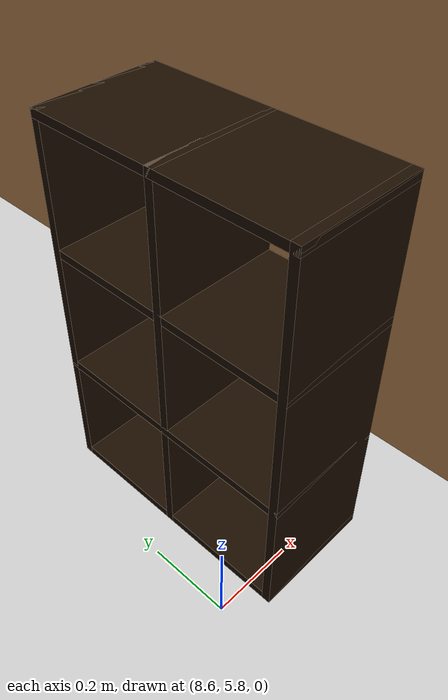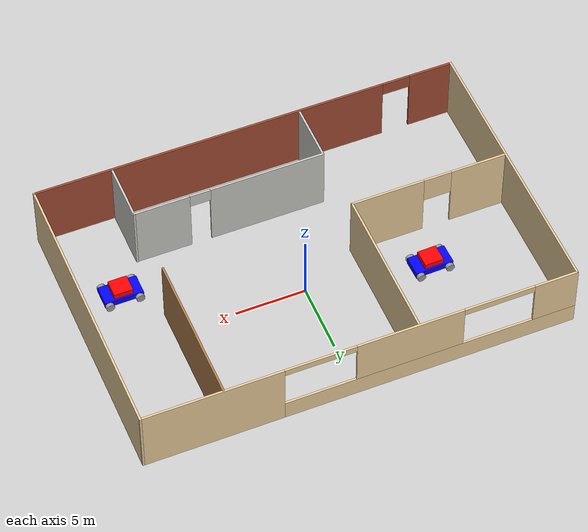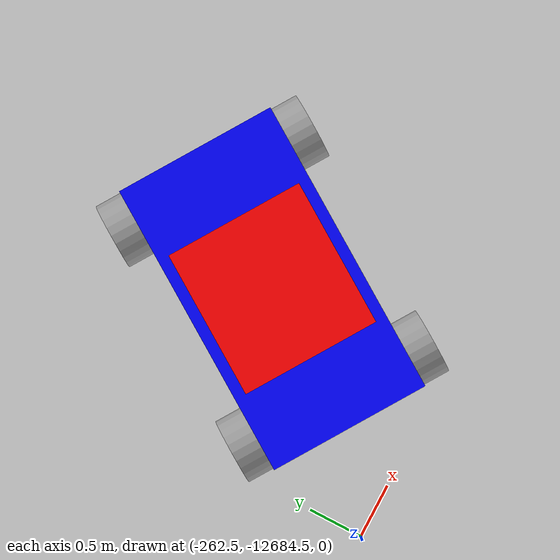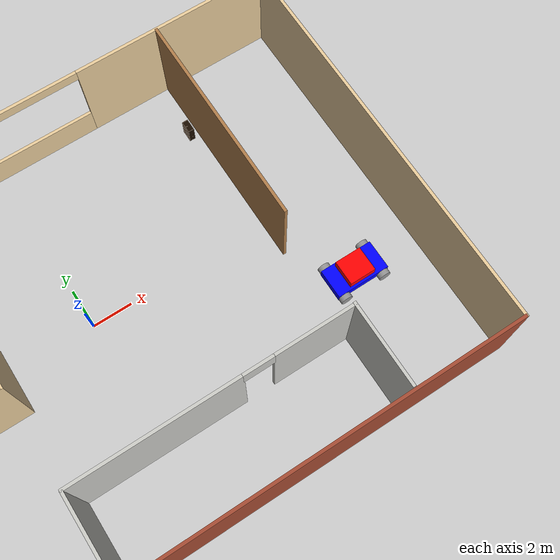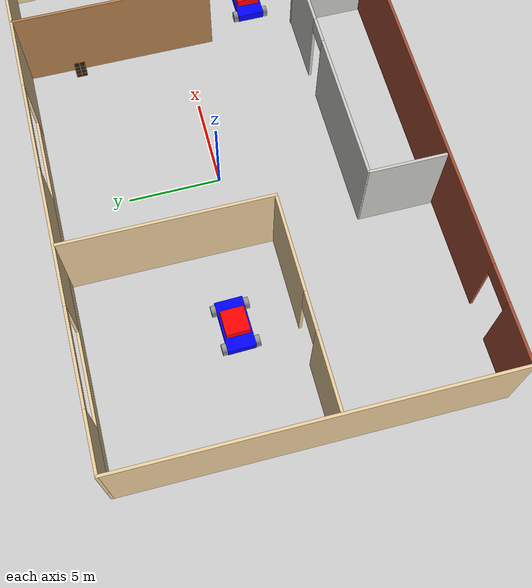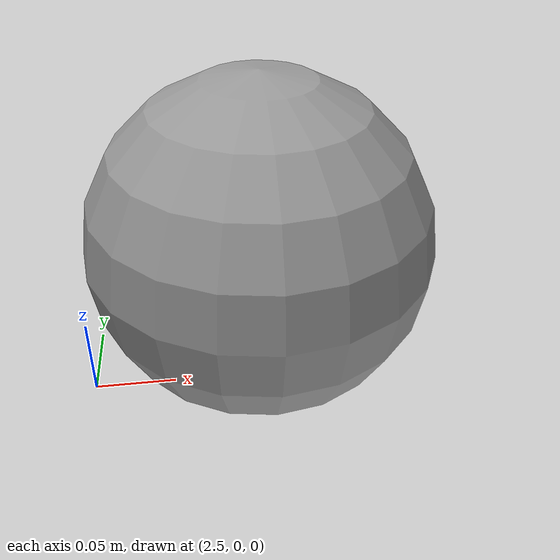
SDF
<sdf version="1.6">
 <world name="default">
  <plugin name="welcome_message.cpp" filename="libwelcome_message.so"/>
  <light name="sun" type="directional">
   <pose>0 0 10 0 -0 0</pose>
   <diffuse>0.8 0.8 0.8 1</diffuse>
   <specular>0.1 0.1 0.1 1</specular>
   <attenuation>
    <range>1000</range>
    <constant>0.9</constant>
    <linear>0.01</linear>
    <quadratic>0.001</quadratic>
   </attenuation>
   <direction>-0.5 0.5 -1</direction>
  </light>
  <model name="ground_plane">
   <static>1</static>
   <link name="link">
    <collision name="collision">
     <geometry><plane><normal>0 0 1</normal><size>100 100</size></plane></geometry>
     <surface><friction><ode><mu>100</mu><mu2>50</mu2></ode></friction></surface>
    </collision>
    <visual name="visual">
     <cast_shadows>0</cast_shadows>
     <geometry><plane><normal>0 0 1</normal><size>100 100</size></plane></geometry>
     <material>
      <script><uri>file://media/materials/scripts/gazebo.material</uri><name>Gazebo/Grey</name></script>
     </material>
    </visual>
   </link>
  </model>
  <gravity>0 0 -9.8</gravity>
  <magnetic_field>6e-06 2.3e-05 -4.2e-05</magnetic_field>
  <atmosphere type="adiabatic"/>
  <physics name="default_physics" default="0" type="ode">
   <max_step_size>0.001</max_step_size>
   <real_time_factor>1</real_time_factor>
   <real_time_update_rate>1000</real_time_update_rate>
  </physics>
  <scene><ambient>0.4 0.4 0.4 1</ambient><background>0.7 0.7 0.7 1</background><shadows>1</shadows></scene>
  <spherical_coordinates>
   <surface_model>EARTH_WGS84</surface_model>
   <latitude_deg>0</latitude_deg>
   <longitude_deg>0</longitude_deg>
   <elevation>0</elevation>
   <heading_deg>0</heading_deg>
  </spherical_coordinates>
  <model name="house_robot">
   <link name="Wall_103">
    <pose>-3.96202 4.4525 0 0 -0 1.5708</pose>
    <visual name="Wall_103_Visual">
     <pose>0 0 2.5 0 -0 0</pose>
     <geometry><box><size>11 0.15 5</size></box></geometry>
     <material>
      <script><uri>file://media/materials/scripts/gazebo.material</uri><name>Gazebo/Grey</name></script>
      <ambient>0.921569 0.807843 0.615686 1</ambient>
      <diffuse>0.7 0.7 0.7 1</diffuse>
      <specular>0.01 0.01 0.01 1</specular>
      <emissive>0 0 0 1</emissive>
     </material>
    </visual>
    <collision name="Wall_103_Collision">
     <pose>0 0 2.5 0 -0 0</pose>
     <geometry><box><size>11 0.15 5</size></box></geometry>
     <surface>
      <friction>
       <ode><mu>1</mu><mu2>1</mu2><fdir1>0 0 0</fdir1><slip1>0</slip1><slip2>0</slip2></ode>
       <torsional>
        <coefficient>1</coefficient>
        <patch_radius>0</patch_radius>
        <surface_radius>0</surface_radius>
        <use_patch_radius>1</use_patch_radius>
        <ode><slip>0</slip></ode>
       </torsional>
      </friction>
      <bounce><restitution_coefficient>0</restitution_coefficient><threshold>1e+06</threshold></bounce>
      <contact>
       <collide_without_contact>0</collide_without_contact>
       <collide_without_contact_bitmask>1</collide_without_contact_bitmask>
       <collide_bitmask>1</collide_bitmask>
       <ode>
        <soft_cfm>0</soft_cfm>
        <soft_erp>0.2</soft_erp>
        <kp>1e+13</kp>
        <kd>1</kd>
        <max_vel>0.01</max_vel>
        <min_depth>0</min_depth>
       </ode>
       <bullet>
        <split_impulse>1</split_impulse>
        <split_impulse_penetration_threshold>-0.01</split_impulse_penetration_threshold>
        <soft_cfm>0</soft_cfm>
        <soft_erp>0.2</soft_erp>
        <kp>1e+13</kp>
        <kd>1</kd>
       </bullet>
      </contact>
     </surface>
    </collision>
   </link>
   <link name="Wall_105">
    <pose>9.54899 4.5795 0 0 0 -1.5708</pose>
    <visual name="Wall_105_Visual">
     <pose>0 0 2.5 0 -0 0</pose>
     <geometry><box><size>10.75 0.15 5</size></box></geometry>
     <material>
      <script><uri>file://media/materials/scripts/gazebo.material</uri><name>Gazebo/Wood</name></script>
      <ambient>0.921569 0.807843 0.615686 1</ambient>
      <diffuse>1 1 1 1</diffuse>
      <specular>0.2 0.2 0.2 1</specular>
      <emissive>0 0 0 1</emissive>
     </material>
    </visual>
    <collision name="Wall_105_Collision">
     <pose>0 0 2.5 0 -0 0</pose>
     <geometry><box><size>10.75 0.15 5</size></box></geometry>
     <surface>
      <friction>
       <ode><mu>1</mu><mu2>1</mu2><fdir1>0 0 0</fdir1><slip1>0</slip1><slip2>0</slip2></ode>
       <torsional>
        <coefficient>1</coefficient>
        <patch_radius>0</patch_radius>
        <surface_radius>0</surface_radius>
        <use_patch_radius>1</use_patch_radius>
        <ode><slip>0</slip></ode>
       </torsional>
      </friction>
      <bounce><restitution_coefficient>0</restitution_coefficient><threshold>1e+06</threshold></bounce>
      <contact>
       <collide_without_contact>0</collide_without_contact>
       <collide_without_contact_bitmask>1</collide_without_contact_bitmask>
       <collide_bitmask>1</collide_bitmask>
       <ode>
        <soft_cfm>0</soft_cfm>
        <soft_erp>0.2</soft_erp>
        <kp>1e+13</kp>
        <kd>1</kd>
        <max_vel>0.01</max_vel>
        <min_depth>0</min_depth>
       </ode>
       <bullet>
        <split_impulse>1</split_impulse>
        <split_impulse_penetration_threshold>-0.01</split_impulse_penetration_threshold>
        <soft_cfm>0</soft_cfm>
        <soft_erp>0.2</soft_erp>
        <kp>1e+13</kp>
        <kd>1</kd>
       </bullet>
      </contact>
     </surface>
    </collision>
   </link>
   <link name="Wall_107">
    <pose>15.175 0.0265 0 0 -0 1.5708</pose>
    <visual name="Wall_107_Visual">
     <pose>0 0 2.5 0 -0 0</pose>
     <geometry><box><size>20 0.15 5</size></box></geometry>
     <material>
      <script><uri>file://media/materials/scripts/gazebo.material</uri><name>Gazebo/Grey</name></script>
      <ambient>0.921569 0.807843 0.615686 1</ambient>
      <diffuse>0.7 0.7 0.7 1</diffuse>
      <specular>0.01 0.01 0.01 1</specular>
      <emissive>0 0 0 1</emissive>
     </material>
    </visual>
    <collision name="Wall_107_Collision">
     <pose>0 0 2.5 0 -0 0</pose>
     <geometry><box><size>20 0.15 5</size></box></geometry>
     <surface>
      <friction>
       <ode><mu>1</mu><mu2>1</mu2><fdir1>0 0 0</fdir1><slip1>0</slip1><slip2>0</slip2></ode>
       <torsional>
        <coefficient>1</coefficient>
        <patch_radius>0</patch_radius>
        <surface_radius>0</surface_radius>
        <use_patch_radius>1</use_patch_radius>
        <ode><slip>0</slip></ode>
       </torsional>
      </friction>
      <bounce><restitution_coefficient>0</restitution_coefficient><threshold>1e+06</threshold></bounce>
      <contact>
       <collide_without_contact>0</collide_without_contact>
       <collide_without_contact_bitmask>1</collide_without_contact_bitmask>
       <collide_bitmask>1</collide_bitmask>
       <ode>
        <soft_cfm>0</soft_cfm>
        <soft_erp>0.2</soft_erp>
        <kp>1e+13</kp>
        <kd>1</kd>
        <max_vel>0.01</max_vel>
        <min_depth>0</min_depth>
       </ode>
       <bullet>
        <split_impulse>1</split_impulse>
        <split_impulse_penetration_threshold>-0.01</split_impulse_penetration_threshold>
        <soft_cfm>0</soft_cfm>
        <soft_erp>0.2</soft_erp>
        <kp>1e+13</kp>
        <kd>1</kd>
       </bullet>
      </contact>
     </surface>
    </collision>
   </link>
   <link name="Wall_108">
    <pose>-1.5e-05 9.9515 0 0 -0 3.14159</pose>
    <visual name="Wall_108_Visual_1">
     <pose>4.92284 0 0.75 0 -0 0</pose>
     <geometry><box><size>20.6543 0.15 1.5</size></box></geometry>
     <material>
      <script><uri>file://media/materials/scripts/gazebo.material</uri><name>Gazebo/Grey</name></script>
      <ambient>0.921569 0.807843 0.615686 1</ambient>
      <diffuse>0.7 0.7 0.7 1</diffuse>
      <specular>0.01 0.01 0.01 1</specular>
      <emissive>0 0 0 1</emissive>
     </material>
    </visual>
    <visual name="Wall_108_Visual_4">
     <pose>-2.90432 0 4.75 0 -0 0</pose>
     <geometry><box><size>5 0.15 0.5</size></box></geometry>
     <material>
      <script><uri>file://media/materials/scripts/gazebo.material</uri><name>Gazebo/Grey</name></script>
      <ambient>0.921569 0.807843 0.615686 1</ambient>
      <diffuse>0.7 0.7 0.7 1</diffuse>
      <specular>0.01 0.01 0.01 1</specular>
      <emissive>0 0 0 1</emissive>
     </material>
    </visual>
    <visual name="Wall_108_Visual_5">
     <pose>9.64746 0 4.75 0 -0 0</pose>
     <geometry><box><size>5 0.15 0.5</size></box></geometry>
     <material>
      <script><uri>file://media/materials/scripts/gazebo.material</uri><name>Gazebo/Grey</name></script>
      <ambient>0.921569 0.807843 0.615686 1</ambient>
      <diffuse>0.7 0.7 0.7 1</diffuse>
      <specular>0.01 0.01 0.01 1</specular>
      <emissive>0 0 0 1</emissive>
     </material>
    </visual>
    <visual name="Wall_108_Visual_2">
     <pose>3.37157 0 3.25 0 -0 0</pose>
     <geometry><box><size>7.55178 0.15 3.5</size></box></geometry>
     <material>
      <script><uri>file://media/materials/scripts/gazebo.material</uri><name>Gazebo/Grey</name></script>
      <ambient>0.921569 0.807843 0.615686 1</ambient>
      <diffuse>0.7 0.7 0.7 1</diffuse>
      <specular>0.01 0.01 0.01 1</specular>
      <emissive>0 0 0 1</emissive>
     </material>
    </visual>
    <visual name="Wall_108_Visual_0">
     <pose>-10.3272 0 2.5 0 -0 0</pose>
     <geometry><box><size>9.84568 0.15 5</size></box></geometry>
     <material>
      <script><uri>file://media/materials/scripts/gazebo.material</uri><name>Gazebo/Grey</name></script>
      <ambient>0.921569 0.807843 0.615686 1</ambient>
      <diffuse>0.7 0.7 0.7 1</diffuse>
      <specular>0.01 0.01 0.01 1</specular>
      <emissive>0 0 0 1</emissive>
     </material>
    </visual>
    <visual name="Wall_108_Visual_3">
     <pose>13.6987 0 3.25 0 -0 0</pose>
     <geometry><box><size>3.10254 0.15 3.5</size></box></geometry>
     <material>
      <script><uri>file://media/materials/scripts/gazebo.material</uri><name>Gazebo/Grey</name></script>
      <ambient>0.921569 0.807843 0.615686 1</ambient>
      <diffuse>0.7 0.7 0.7 1</diffuse>
      <specular>0.01 0.01 0.01 1</specular>
      <emissive>0 0 0 1</emissive>
     </material>
    </visual>
    <collision name="Wall_108_Collision_0">
     <pose>-10.3272 0 2.5 0 -0 0</pose>
     <geometry><box><size>9.84568 0.15 5</size></box></geometry>
     <surface>
      <friction>
       <ode><mu>1</mu><mu2>1</mu2><fdir1>0 0 0</fdir1><slip1>0</slip1><slip2>0</slip2></ode>
       <torsional>
        <coefficient>1</coefficient>
        <patch_radius>0</patch_radius>
        <surface_radius>0</surface_radius>
        <use_patch_radius>1</use_patch_radius>
        <ode><slip>0</slip></ode>
       </torsional>
      </friction>
      <bounce><restitution_coefficient>0</restitution_coefficient><threshold>1e+06</threshold></bounce>
      <contact>
       <collide_without_contact>0</collide_without_contact>
       <collide_without_contact_bitmask>1</collide_without_contact_bitmask>
       <collide_bitmask>1</collide_bitmask>
       <ode>
        <soft_cfm>0</soft_cfm>
        <soft_erp>0.2</soft_erp>
        <kp>1e+13</kp>
        <kd>1</kd>
        <max_vel>0.01</max_vel>
        <min_depth>0</min_depth>
       </ode>
       <bullet>
        <split_impulse>1</split_impulse>
        <split_impulse_penetration_threshold>-0.01</split_impulse_penetration_threshold>
        <soft_cfm>0</soft_cfm>
        <soft_erp>0.2</soft_erp>
        <kp>1e+13</kp>
        <kd>1</kd>
       </bullet>
      </contact>
     </surface>
    </collision>
    <collision name="Wall_108_Collision_1">
     <pose>4.92284 0 0.75 0 -0 0</pose>
     <geometry><box><size>20.6543 0.15 1.5</size></box></geometry>
     <surface>
      <friction>
       <ode><mu>1</mu><mu2>1</mu2><fdir1>0 0 0</fdir1><slip1>0</slip1><slip2>0</slip2></ode>
       <torsional>
        <coefficient>1</coefficient>
        <patch_radius>0</patch_radius>
        <surface_radius>0</surface_radius>
        <use_patch_radius>1</use_patch_radius>
        <ode><slip>0</slip></ode>
       </torsional>
      </friction>
      <bounce><restitution_coefficient>0</restitution_coefficient><threshold>1e+06</threshold></bounce>
      <contact>
       <collide_without_contact>0</collide_without_contact>
       <collide_without_contact_bitmask>1</collide_without_contact_bitmask>
       <collide_bitmask>1</collide_bitmask>
       <ode>
        <soft_cfm>0</soft_cfm>
        <soft_erp>0.2</soft_erp>
        <kp>1e+13</kp>
        <kd>1</kd>
        <max_vel>0.01</max_vel>
        <min_depth>0</min_depth>
       </ode>
       <bullet>
        <split_impulse>1</split_impulse>
        <split_impulse_penetration_threshold>-0.01</split_impulse_penetration_threshold>
        <soft_cfm>0</soft_cfm>
        <soft_erp>0.2</soft_erp>
        <kp>1e+13</kp>
        <kd>1</kd>
       </bullet>
      </contact>
     </surface>
    </collision>
    <collision name="Wall_108_Collision_4">
     <pose>-2.90432 0 4.75 0 -0 0</pose>
     <geometry><box><size>5 0.15 0.5</size></box></geometry>
     <surface>
      <friction>
       <ode><mu>1</mu><mu2>1</mu2><fdir1>0 0 0</fdir1><slip1>0</slip1><slip2>0</slip2></ode>
       <torsional>
        <coefficient>1</coefficient>
        <patch_radius>0</patch_radius>
        <surface_radius>0</surface_radius>
        <use_patch_radius>1</use_patch_radius>
        <ode><slip>0</slip></ode>
       </torsional>
      </friction>
      <bounce><restitution_coefficient>0</restitution_coefficient><threshold>1e+06</threshold></bounce>
      <contact>
       <collide_without_contact>0</collide_without_contact>
       <collide_without_contact_bitmask>1</collide_without_contact_bitmask>
       <collide_bitmask>1</collide_bitmask>
       <ode>
        <soft_cfm>0</soft_cfm>
        <soft_erp>0.2</soft_erp>
        <kp>1e+13</kp>
        <kd>1</kd>
        <max_vel>0.01</max_vel>
        <min_depth>0</min_depth>
       </ode>
       <bullet>
        <split_impulse>1</split_impulse>
        <split_impulse_penetration_threshold>-0.01</split_impulse_penetration_threshold>
        <soft_cfm>0</soft_cfm>
        <soft_erp>0.2</soft_erp>
        <kp>1e+13</kp>
        <kd>1</kd>
       </bullet>
      </contact>
     </surface>
    </collision>
    <collision name="Wall_108_Collision_2">
     <pose>3.37157 0 3.25 0 -0 0</pose>
     <geometry><box><size>7.55178 0.15 3.5</size></box></geometry>
     <surface>
      <friction>
       <ode><mu>1</mu><mu2>1</mu2><fdir1>0 0 0</fdir1><slip1>0</slip1><slip2>0</slip2></ode>
       <torsional>
        <coefficient>1</coefficient>
        <patch_radius>0</patch_radius>
        <surface_radius>0</surface_radius>
        <use_patch_radius>1</use_patch_radius>
        <ode><slip>0</slip></ode>
       </torsional>
      </friction>
      <bounce><restitution_coefficient>0</restitution_coefficient><threshold>1e+06</threshold></bounce>
      <contact>
       <collide_without_contact>0</collide_without_contact>
       <collide_without_contact_bitmask>1</collide_without_contact_bitmask>
       <collide_bitmask>1</collide_bitmask>
       <ode>
        <soft_cfm>0</soft_cfm>
        <soft_erp>0.2</soft_erp>
        <kp>1e+13</kp>
        <kd>1</kd>
        <max_vel>0.01</max_vel>
        <min_depth>0</min_depth>
       </ode>
       <bullet>
        <split_impulse>1</split_impulse>
        <split_impulse_penetration_threshold>-0.01</split_impulse_penetration_threshold>
        <soft_cfm>0</soft_cfm>
        <soft_erp>0.2</soft_erp>
        <kp>1e+13</kp>
        <kd>1</kd>
       </bullet>
      </contact>
     </surface>
    </collision>
    <collision name="Wall_108_Collision_3">
     <pose>13.6987 0 3.25 0 -0 0</pose>
     <geometry><box><size>3.10254 0.15 3.5</size></box></geometry>
     <surface>
      <friction>
       <ode><mu>1</mu><mu2>1</mu2><fdir1>0 0 0</fdir1><slip1>0</slip1><slip2>0</slip2></ode>
       <torsional>
        <coefficient>1</coefficient>
        <patch_radius>0</patch_radius>
        <surface_radius>0</surface_radius>
        <use_patch_radius>1</use_patch_radius>
        <ode><slip>0</slip></ode>
       </torsional>
      </friction>
      <bounce><restitution_coefficient>0</restitution_coefficient><threshold>1e+06</threshold></bounce>
      <contact>
       <collide_without_contact>0</collide_without_contact>
       <collide_without_contact_bitmask>1</collide_without_contact_bitmask>
       <collide_bitmask>1</collide_bitmask>
       <ode>
        <soft_cfm>0</soft_cfm>
        <soft_erp>0.2</soft_erp>
        <kp>1e+13</kp>
        <kd>1</kd>
        <max_vel>0.01</max_vel>
        <min_depth>0</min_depth>
       </ode>
       <bullet>
        <split_impulse>1</split_impulse>
        <split_impulse_penetration_threshold>-0.01</split_impulse_penetration_threshold>
        <soft_cfm>0</soft_cfm>
        <soft_erp>0.2</soft_erp>
        <kp>1e+13</kp>
        <kd>1</kd>
       </bullet>
      </contact>
     </surface>
    </collision>
    <collision name="Wall_108_Collision_5">
     <pose>9.64746 0 4.75 0 -0 0</pose>
     <geometry><box><size>5 0.15 0.5</size></box></geometry>
     <surface>
      <friction>
       <ode><mu>1</mu><mu2>1</mu2><fdir1>0 0 0</fdir1><slip1>0</slip1><slip2>0</slip2></ode>
       <torsional>
        <coefficient>1</coefficient>
        <patch_radius>0</patch_radius>
        <surface_radius>0</surface_radius>
        <use_patch_radius>1</use_patch_radius>
        <ode><slip>0</slip></ode>
       </torsional>
      </friction>
      <bounce><restitution_coefficient>0</restitution_coefficient><threshold>1e+06</threshold></bounce>
      <contact>
       <collide_without_contact>0</collide_without_contact>
       <collide_without_contact_bitmask>1</collide_without_contact_bitmask>
       <collide_bitmask>1</collide_bitmask>
       <ode>
        <soft_cfm>0</soft_cfm>
        <soft_erp>0.2</soft_erp>
        <kp>1e+13</kp>
        <kd>1</kd>
        <max_vel>0.01</max_vel>
        <min_depth>0</min_depth>
       </ode>
       <bullet>
        <split_impulse>1</split_impulse>
        <split_impulse_penetration_threshold>-0.01</split_impulse_penetration_threshold>
        <soft_cfm>0</soft_cfm>
        <soft_erp>0.2</soft_erp>
        <kp>1e+13</kp>
        <kd>1</kd>
       </bullet>
      </contact>
     </surface>
    </collision>
   </link>
   <link name="Wall_109">
    <pose>-15.175 0.0265 0 0 0 -1.5708</pose>
    <visual name="Wall_109_Visual">
     <pose>0 0 2.5 0 -0 0</pose>
     <geometry><box><size>20 0.15 5</size></box></geometry>
     <material>
      <script><uri>file://media/materials/scripts/gazebo.material</uri><name>Gazebo/Grey</name></script>
      <ambient>0.921569 0.807843 0.615686 1</ambient>
      <diffuse>0.7 0.7 0.7 1</diffuse>
      <specular>0.01 0.01 0.01 1</specular>
      <emissive>0 0 0 1</emissive>
     </material>
    </visual>
    <collision name="Wall_109_Collision">
     <pose>0 0 2.5 0 -0 0</pose>
     <geometry><box><size>20 0.15 5</size></box></geometry>
     <surface>
      <friction>
       <ode><mu>1</mu><mu2>1</mu2><fdir1>0 0 0</fdir1><slip1>0</slip1><slip2>0</slip2></ode>
       <torsional>
        <coefficient>1</coefficient>
        <patch_radius>0</patch_radius>
        <surface_radius>0</surface_radius>
        <use_patch_radius>1</use_patch_radius>
        <ode><slip>0</slip></ode>
       </torsional>
      </friction>
      <bounce><restitution_coefficient>0</restitution_coefficient><threshold>1e+06</threshold></bounce>
      <contact>
       <collide_without_contact>0</collide_without_contact>
       <collide_without_contact_bitmask>1</collide_without_contact_bitmask>
       <collide_bitmask>1</collide_bitmask>
       <ode>
        <soft_cfm>0</soft_cfm>
        <soft_erp>0.2</soft_erp>
        <kp>1e+13</kp>
        <kd>1</kd>
        <max_vel>0.01</max_vel>
        <min_depth>0</min_depth>
       </ode>
       <bullet>
        <split_impulse>1</split_impulse>
        <split_impulse_penetration_threshold>-0.01</split_impulse_penetration_threshold>
        <soft_cfm>0</soft_cfm>
        <soft_erp>0.2</soft_erp>
        <kp>1e+13</kp>
        <kd>1</kd>
       </bullet>
      </contact>
     </surface>
    </collision>
   </link>
   <link name="Wall_119">
    <pose>9.67953 -7.71239 0 0 -0 1.5708</pose>
    <inertial>
     <inertia><ixx>nan</ixx><ixy>0</ixy><ixz>0</ixz><iyy>nan</iyy><iyz>0</iyz><izz>nan</izz></inertia>
     <mass>0</mass>
    </inertial>
    <visual name="Wall_119_Visual">
     <pose>0 0 2.5 0 -0 0</pose>
     <geometry><box><size>4.17951 0.15 5</size></box></geometry>
     <material>
      <script><uri>file://media/materials/scripts/gazebo.material</uri><name>Gazebo/CeilingTiled</name></script>
      <ambient>0.921569 0.807843 0.615686 1</ambient>
      <diffuse>1 1 1 1</diffuse>
      <specular>0 0 0 1</specular>
      <emissive>0 0 0 1</emissive>
     </material>
    </visual>
    <collision name="Wall_119_Collision">
     <pose>0 0 2.5 0 -0 0</pose>
     <geometry><box><size>4.17951 0.15 5</size></box></geometry>
     <surface>
      <friction>
       <ode><mu>1</mu><mu2>1</mu2><fdir1>0 0 0</fdir1><slip1>0</slip1><slip2>0</slip2></ode>
       <torsional>
        <coefficient>1</coefficient>
        <patch_radius>0</patch_radius>
        <surface_radius>0</surface_radius>
        <use_patch_radius>1</use_patch_radius>
        <ode><slip>0</slip></ode>
       </torsional>
      </friction>
      <bounce><restitution_coefficient>0</restitution_coefficient><threshold>1e+06</threshold></bounce>
      <contact>
       <collide_without_contact>0</collide_without_contact>
       <collide_without_contact_bitmask>1</collide_without_contact_bitmask>
       <collide_bitmask>1</collide_bitmask>
       <ode>
        <soft_cfm>0</soft_cfm>
        <soft_erp>0.2</soft_erp>
        <kp>1e+13</kp>
        <kd>1</kd>
        <max_vel>0.01</max_vel>
        <min_depth>0</min_depth>
       </ode>
       <bullet>
        <split_impulse>1</split_impulse>
        <split_impulse_penetration_threshold>-0.01</split_impulse_penetration_threshold>
        <soft_cfm>0</soft_cfm>
        <soft_erp>0.2</soft_erp>
        <kp>1e+13</kp>
        <kd>1</kd>
       </bullet>
      </contact>
     </surface>
    </collision>
   </link>
   <link name="Wall_120">
    <pose>2.89875 -5.72264 0 0 -0 3.14159</pose>
    <inertial>
     <inertia><ixx>nan</ixx><ixy>0</ixy><ixz>0</ixz><iyy>nan</iyy><iyz>0</iyz><izz>nan</izz></inertia>
     <mass>0</mass>
    </inertial>
    <visual name="Wall_120_Visual_0">
     <pose>-4.81655 0 2.5 0 -0 0</pose>
     <geometry><box><size>3.97669 0.15 5</size></box></geometry>
     <material>
      <script><uri>file://media/materials/scripts/gazebo.material</uri><name>Gazebo/CeilingTiled</name></script>
      <ambient>0.921569 0.807843 0.615686 1</ambient>
      <diffuse>1 1 1 1</diffuse>
      <specular>0 0 0 1</specular>
      <emissive>0 0 0 1</emissive>
     </material>
    </visual>
    <visual name="Wall_120_Visual_1">
     <pose>2.71536 0 2.5 0 -0 0</pose>
     <geometry><box><size>8.22824 0.15 5</size></box></geometry>
     <material>
      <script><uri>file://media/materials/scripts/gazebo.material</uri><name>Gazebo/CeilingTiled</name></script>
      <ambient>0.921569 0.807843 0.615686 1</ambient>
      <diffuse>1 1 1 1</diffuse>
      <specular>0 0 0 1</specular>
      <emissive>0 0 0 1</emissive>
     </material>
    </visual>
    <visual name="Wall_120_Visual_2">
     <pose>-2.10119 0 4.5 0 -0 0</pose>
     <geometry><box><size>1.51755 0.15 1</size></box></geometry>
     <material>
      <script><uri>file://media/materials/scripts/gazebo.material</uri><name>Gazebo/CeilingTiled</name></script>
      <ambient>0.921569 0.807843 0.615686 1</ambient>
      <diffuse>1 1 1 1</diffuse>
      <specular>0 0 0 1</specular>
      <emissive>0 0 0 1</emissive>
     </material>
    </visual>
    <collision name="Wall_120_Collision_2">
     <pose>-2.10119 0 4.5 0 -0 0</pose>
     <geometry><box><size>1.51755 0.15 1</size></box></geometry>
     <surface>
      <friction>
       <ode><mu>1</mu><mu2>1</mu2><fdir1>0 0 0</fdir1><slip1>0</slip1><slip2>0</slip2></ode>
       <torsional>
        <coefficient>1</coefficient>
        <patch_radius>0</patch_radius>
        <surface_radius>0</surface_radius>
        <use_patch_radius>1</use_patch_radius>
        <ode><slip>0</slip></ode>
       </torsional>
      </friction>
      <bounce><restitution_coefficient>0</restitution_coefficient><threshold>1e+06</threshold></bounce>
      <contact>
       <collide_without_contact>0</collide_without_contact>
       <collide_without_contact_bitmask>1</collide_without_contact_bitmask>
       <collide_bitmask>1</collide_bitmask>
       <ode>
        <soft_cfm>0</soft_cfm>
        <soft_erp>0.2</soft_erp>
        <kp>1e+13</kp>
        <kd>1</kd>
        <max_vel>0.01</max_vel>
        <min_depth>0</min_depth>
       </ode>
       <bullet>
        <split_impulse>1</split_impulse>
        <split_impulse_penetration_threshold>-0.01</split_impulse_penetration_threshold>
        <soft_cfm>0</soft_cfm>
        <soft_erp>0.2</soft_erp>
        <kp>1e+13</kp>
        <kd>1</kd>
       </bullet>
      </contact>
     </surface>
    </collision>
    <collision name="Wall_120_Collision_0">
     <pose>-4.81655 0 2.5 0 -0 0</pose>
     <geometry><box><size>3.97669 0.15 5</size></box></geometry>
     <surface>
      <friction>
       <ode><mu>1</mu><mu2>1</mu2><fdir1>0 0 0</fdir1><slip1>0</slip1><slip2>0</slip2></ode>
       <torsional>
        <coefficient>1</coefficient>
        <patch_radius>0</patch_radius>
        <surface_radius>0</surface_radius>
        <use_patch_radius>1</use_patch_radius>
        <ode><slip>0</slip></ode>
       </torsional>
      </friction>
      <bounce><restitution_coefficient>0</restitution_coefficient><threshold>1e+06</threshold></bounce>
      <contact>
       <collide_without_contact>0</collide_without_contact>
       <collide_without_contact_bitmask>1</collide_without_contact_bitmask>
       <collide_bitmask>1</collide_bitmask>
       <ode>
        <soft_cfm>0</soft_cfm>
        <soft_erp>0.2</soft_erp>
        <kp>1e+13</kp>
        <kd>1</kd>
        <max_vel>0.01</max_vel>
        <min_depth>0</min_depth>
       </ode>
       <bullet>
        <split_impulse>1</split_impulse>
        <split_impulse_penetration_threshold>-0.01</split_impulse_penetration_threshold>
        <soft_cfm>0</soft_cfm>
        <soft_erp>0.2</soft_erp>
        <kp>1e+13</kp>
        <kd>1</kd>
       </bullet>
      </contact>
     </surface>
    </collision>
    <collision name="Wall_120_Collision_1">
     <pose>2.71536 0 2.5 0 -0 0</pose>
     <geometry><box><size>8.22824 0.15 5</size></box></geometry>
     <surface>
      <friction>
       <ode><mu>1</mu><mu2>1</mu2><fdir1>0 0 0</fdir1><slip1>0</slip1><slip2>0</slip2></ode>
       <torsional>
        <coefficient>1</coefficient>
        <patch_radius>0</patch_radius>
        <surface_radius>0</surface_radius>
        <use_patch_radius>1</use_patch_radius>
        <ode><slip>0</slip></ode>
       </torsional>
      </friction>
      <bounce><restitution_coefficient>0</restitution_coefficient><threshold>1e+06</threshold></bounce>
      <contact>
       <collide_without_contact>0</collide_without_contact>
       <collide_without_contact_bitmask>1</collide_without_contact_bitmask>
       <collide_bitmask>1</collide_bitmask>
       <ode>
        <soft_cfm>0</soft_cfm>
        <soft_erp>0.2</soft_erp>
        <kp>1e+13</kp>
        <kd>1</kd>
        <max_vel>0.01</max_vel>
        <min_depth>0</min_depth>
       </ode>
       <bullet>
        <split_impulse>1</split_impulse>
        <split_impulse_penetration_threshold>-0.01</split_impulse_penetration_threshold>
        <soft_cfm>0</soft_cfm>
        <soft_erp>0.2</soft_erp>
        <kp>1e+13</kp>
        <kd>1</kd>
       </bullet>
      </contact>
     </surface>
    </collision>
   </link>
   <link name="Wall_121">
    <pose>-3.87202 -7.75642 0 0 0 -1.5708</pose>
    <inertial>
     <inertia><ixx>nan</ixx><ixy>0</ixy><ixz>0</ixz><iyy>nan</iyy><iyz>0</iyz><izz>nan</izz></inertia>
     <mass>0</mass>
    </inertial>
    <visual name="Wall_121_Visual">
     <pose>0 0 2.5 0 -0 0</pose>
     <geometry><box><size>4.07058 0.15 5</size></box></geometry>
     <material>
      <script><uri>file://media/materials/scripts/gazebo.material</uri><name>Gazebo/CeilingTiled</name></script>
      <ambient>0.921569 0.807843 0.615686 1</ambient>
      <diffuse>1 1 1 1</diffuse>
      <specular>0 0 0 1</specular>
      <emissive>0 0 0 1</emissive>
     </material>
    </visual>
    <collision name="Wall_121_Collision">
     <pose>0 0 2.5 0 -0 0</pose>
     <geometry><box><size>4.07058 0.15 5</size></box></geometry>
     <surface>
      <friction>
       <ode><mu>1</mu><mu2>1</mu2><fdir1>0 0 0</fdir1><slip1>0</slip1><slip2>0</slip2></ode>
       <torsional>
        <coefficient>1</coefficient>
        <patch_radius>0</patch_radius>
        <surface_radius>0</surface_radius>
        <use_patch_radius>1</use_patch_radius>
        <ode><slip>0</slip></ode>
       </torsional>
      </friction>
      <bounce><restitution_coefficient>0</restitution_coefficient><threshold>1e+06</threshold></bounce>
      <contact>
       <collide_without_contact>0</collide_without_contact>
       <collide_without_contact_bitmask>1</collide_without_contact_bitmask>
       <collide_bitmask>1</collide_bitmask>
       <ode>
        <soft_cfm>0</soft_cfm>
        <soft_erp>0.2</soft_erp>
        <kp>1e+13</kp>
        <kd>1</kd>
        <max_vel>0.01</max_vel>
        <min_depth>0</min_depth>
       </ode>
       <bullet>
        <split_impulse>1</split_impulse>
        <split_impulse_penetration_threshold>-0.01</split_impulse_penetration_threshold>
        <soft_cfm>0</soft_cfm>
        <soft_erp>0.2</soft_erp>
        <kp>1e+13</kp>
        <kd>1</kd>
       </bullet>
      </contact>
     </surface>
    </collision>
   </link>
   <link name="Wall_50">
    <pose>1.6e-05 -9.8985 0 0 -0 3.14159</pose>
    <visual name="Wall_50_Visual_0">
     <pose>-2.59234 0 2.5 0 -0 0</pose>
     <geometry><box><size>25.3153 0.15 5</size></box></geometry>
     <material>
      <script><uri>file://media/materials/scripts/gazebo.material</uri><name>Gazebo/Bricks</name></script>
      <ambient>1 1 1 1</ambient>
      <diffuse>1 1 1 1</diffuse>
      <specular>0.2 0.2 0.2 1</specular>
      <emissive>0 0 0 1</emissive>
     </material>
    </visual>
    <visual name="Wall_50_Visual_1">
     <pose>13.6577 0 2.5 0 -0 0</pose>
     <geometry><box><size>3.18469 0.15 5</size></box></geometry>
     <material>
      <script><uri>file://media/materials/scripts/gazebo.material</uri><name>Gazebo/Bricks</name></script>
      <ambient>1 1 1 1</ambient>
      <diffuse>1 1 1 1</diffuse>
      <specular>0.2 0.2 0.2 1</specular>
      <emissive>0 0 0 1</emissive>
     </material>
    </visual>
    <visual name="Wall_50_Visual_2">
     <pose>11.0653 0 4.5 0 -0 0</pose>
     <geometry><box><size>2 0.15 1</size></box></geometry>
     <material>
      <script><uri>file://media/materials/scripts/gazebo.material</uri><name>Gazebo/Bricks</name></script>
      <ambient>1 1 1 1</ambient>
      <diffuse>1 1 1 1</diffuse>
      <specular>0.2 0.2 0.2 1</specular>
      <emissive>0 0 0 1</emissive>
     </material>
    </visual>
    <collision name="Wall_50_Collision_0">
     <pose>-2.59234 0 2.5 0 -0 0</pose>
     <geometry><box><size>25.3153 0.15 5</size></box></geometry>
     <surface>
      <friction>
       <ode><mu>1</mu><mu2>1</mu2><fdir1>0 0 0</fdir1><slip1>0</slip1><slip2>0</slip2></ode>
       <torsional>
        <coefficient>1</coefficient>
        <patch_radius>0</patch_radius>
        <surface_radius>0</surface_radius>
        <use_patch_radius>1</use_patch_radius>
        <ode><slip>0</slip></ode>
       </torsional>
      </friction>
      <bounce><restitution_coefficient>0</restitution_coefficient><threshold>1e+06</threshold></bounce>
      <contact>
       <collide_without_contact>0</collide_without_contact>
       <collide_without_contact_bitmask>1</collide_without_contact_bitmask>
       <collide_bitmask>1</collide_bitmask>
       <ode>
        <soft_cfm>0</soft_cfm>
        <soft_erp>0.2</soft_erp>
        <kp>1e+13</kp>
        <kd>1</kd>
        <max_vel>0.01</max_vel>
        <min_depth>0</min_depth>
       </ode>
       <bullet>
        <split_impulse>1</split_impulse>
        <split_impulse_penetration_threshold>-0.01</split_impulse_penetration_threshold>
        <soft_cfm>0</soft_cfm>
        <soft_erp>0.2</soft_erp>
        <kp>1e+13</kp>
        <kd>1</kd>
       </bullet>
      </contact>
     </surface>
    </collision>
    <collision name="Wall_50_Collision_1">
     <pose>13.6577 0 2.5 0 -0 0</pose>
     <geometry><box><size>3.18469 0.15 5</size></box></geometry>
     <surface>
      <friction>
       <ode><mu>1</mu><mu2>1</mu2><fdir1>0 0 0</fdir1><slip1>0</slip1><slip2>0</slip2></ode>
       <torsional>
        <coefficient>1</coefficient>
        <patch_radius>0</patch_radius>
        <surface_radius>0</surface_radius>
        <use_patch_radius>1</use_patch_radius>
        <ode><slip>0</slip></ode>
       </torsional>
      </friction>
      <bounce><restitution_coefficient>0</restitution_coefficient><threshold>1e+06</threshold></bounce>
      <contact>
       <collide_without_contact>0</collide_without_contact>
       <collide_without_contact_bitmask>1</collide_without_contact_bitmask>
       <collide_bitmask>1</collide_bitmask>
       <ode>
        <soft_cfm>0</soft_cfm>
        <soft_erp>0.2</soft_erp>
        <kp>1e+13</kp>
        <kd>1</kd>
        <max_vel>0.01</max_vel>
        <min_depth>0</min_depth>
       </ode>
       <bullet>
        <split_impulse>1</split_impulse>
        <split_impulse_penetration_threshold>-0.01</split_impulse_penetration_threshold>
        <soft_cfm>0</soft_cfm>
        <soft_erp>0.2</soft_erp>
        <kp>1e+13</kp>
        <kd>1</kd>
       </bullet>
      </contact>
     </surface>
    </collision>
    <collision name="Wall_50_Collision_2">
     <pose>11.0653 0 4.5 0 -0 0</pose>
     <geometry><box><size>2 0.15 1</size></box></geometry>
     <surface>
      <friction>
       <ode><mu>1</mu><mu2>1</mu2><fdir1>0 0 0</fdir1><slip1>0</slip1><slip2>0</slip2></ode>
       <torsional>
        <coefficient>1</coefficient>
        <patch_radius>0</patch_radius>
        <surface_radius>0</surface_radius>
        <use_patch_radius>1</use_patch_radius>
        <ode><slip>0</slip></ode>
       </torsional>
      </friction>
      <bounce><restitution_coefficient>0</restitution_coefficient><threshold>1e+06</threshold></bounce>
      <contact>
       <collide_without_contact>0</collide_without_contact>
       <collide_without_contact_bitmask>1</collide_without_contact_bitmask>
       <collide_bitmask>1</collide_bitmask>
       <ode>
        <soft_cfm>0</soft_cfm>
        <soft_erp>0.2</soft_erp>
        <kp>1e+13</kp>
        <kd>1</kd>
        <max_vel>0.01</max_vel>
        <min_depth>0</min_depth>
       </ode>
       <bullet>
        <split_impulse>1</split_impulse>
        <split_impulse_penetration_threshold>-0.01</split_impulse_penetration_threshold>
        <soft_cfm>0</soft_cfm>
        <soft_erp>0.2</soft_erp>
        <kp>1e+13</kp>
        <kd>1</kd>
       </bullet>
      </contact>
     </surface>
    </collision>
   </link>
   <link name="Wall_92">
    <pose>-9.51201 -0.9725 0 0 -0 0</pose>
    <visual name="Wall_92_Visual_0">
     <pose>-3.6411 0 2.5 0 -0 0</pose>
     <geometry><box><size>3.96779 0.15 5</size></box></geometry>
     <material>
      <script><uri>file://media/materials/scripts/gazebo.material</uri><name>Gazebo/Grey</name></script>
      <ambient>0.921569 0.807843 0.615686 1</ambient>
      <diffuse>0.7 0.7 0.7 1</diffuse>
      <specular>0.01 0.01 0.01 1</specular>
      <emissive>0 0 0 1</emissive>
     </material>
    </visual>
    <visual name="Wall_92_Visual_2">
     <pose>-0.657207 0 4 0 -0 0</pose>
     <geometry><box><size>2 0.15 2</size></box></geometry>
     <material>
      <script><uri>file://media/materials/scripts/gazebo.material</uri><name>Gazebo/Grey</name></script>
      <ambient>0.921569 0.807843 0.615686 1</ambient>
      <diffuse>0.7 0.7 0.7 1</diffuse>
      <specular>0.01 0.01 0.01 1</specular>
      <emissive>0 0 0 1</emissive>
     </material>
    </visual>
    <visual name="Wall_92_Visual_1">
     <pose>2.9839 0 2.5 0 -0 0</pose>
     <geometry><box><size>5.28221 0.15 5</size></box></geometry>
     <material>
      <script><uri>file://media/materials/scripts/gazebo.material</uri><name>Gazebo/Grey</name></script>
      <ambient>0.921569 0.807843 0.615686 1</ambient>
      <diffuse>0.7 0.7 0.7 1</diffuse>
      <specular>0.01 0.01 0.01 1</specular>
      <emissive>0 0 0 1</emissive>
     </material>
    </visual>
    <collision name="Wall_92_Collision_0">
     <pose>-3.6411 0 2.5 0 -0 0</pose>
     <geometry><box><size>3.96779 0.15 5</size></box></geometry>
     <surface>
      <friction>
       <ode><mu>1</mu><mu2>1</mu2><fdir1>0 0 0</fdir1><slip1>0</slip1><slip2>0</slip2></ode>
       <torsional>
        <coefficient>1</coefficient>
        <patch_radius>0</patch_radius>
        <surface_radius>0</surface_radius>
        <use_patch_radius>1</use_patch_radius>
        <ode><slip>0</slip></ode>
       </torsional>
      </friction>
      <bounce><restitution_coefficient>0</restitution_coefficient><threshold>1e+06</threshold></bounce>
      <contact>
       <collide_without_contact>0</collide_without_contact>
       <collide_without_contact_bitmask>1</collide_without_contact_bitmask>
       <collide_bitmask>1</collide_bitmask>
       <ode>
        <soft_cfm>0</soft_cfm>
        <soft_erp>0.2</soft_erp>
        <kp>1e+13</kp>
        <kd>1</kd>
        <max_vel>0.01</max_vel>
        <min_depth>0</min_depth>
       </ode>
       <bullet>
        <split_impulse>1</split_impulse>
        <split_impulse_penetration_threshold>-0.01</split_impulse_penetration_threshold>
        <soft_cfm>0</soft_cfm>
        <soft_erp>0.2</soft_erp>
        <kp>1e+13</kp>
        <kd>1</kd>
       </bullet>
      </contact>
     </surface>
    </collision>
    <collision name="Wall_92_Collision_2">
     <pose>-0.657207 0 4 0 -0 0</pose>
     <geometry><box><size>2 0.15 2</size></box></geometry>
     <surface>
      <friction>
       <ode><mu>1</mu><mu2>1</mu2><fdir1>0 0 0</fdir1><slip1>0</slip1><slip2>0</slip2></ode>
       <torsional>
        <coefficient>1</coefficient>
        <patch_radius>0</patch_radius>
        <surface_radius>0</surface_radius>
        <use_patch_radius>1</use_patch_radius>
        <ode><slip>0</slip></ode>
       </torsional>
      </friction>
      <bounce><restitution_coefficient>0</restitution_coefficient><threshold>1e+06</threshold></bounce>
      <contact>
       <collide_without_contact>0</collide_without_contact>
       <collide_without_contact_bitmask>1</collide_without_contact_bitmask>
       <collide_bitmask>1</collide_bitmask>
       <ode>
        <soft_cfm>0</soft_cfm>
        <soft_erp>0.2</soft_erp>
        <kp>1e+13</kp>
        <kd>1</kd>
        <max_vel>0.01</max_vel>
        <min_depth>0</min_depth>
       </ode>
       <bullet>
        <split_impulse>1</split_impulse>
        <split_impulse_penetration_threshold>-0.01</split_impulse_penetration_threshold>
        <soft_cfm>0</soft_cfm>
        <soft_erp>0.2</soft_erp>
        <kp>1e+13</kp>
        <kd>1</kd>
       </bullet>
      </contact>
     </surface>
    </collision>
    <collision name="Wall_92_Collision_1">
     <pose>2.9839 0 2.5 0 -0 0</pose>
     <geometry><box><size>5.28221 0.15 5</size></box></geometry>
     <surface>
      <friction>
       <ode><mu>1</mu><mu2>1</mu2><fdir1>0 0 0</fdir1><slip1>0</slip1><slip2>0</slip2></ode>
       <torsional>
        <coefficient>1</coefficient>
        <patch_radius>0</patch_radius>
        <surface_radius>0</surface_radius>
        <use_patch_radius>1</use_patch_radius>
        <ode><slip>0</slip></ode>
       </torsional>
      </friction>
      <bounce><restitution_coefficient>0</restitution_coefficient><threshold>1e+06</threshold></bounce>
      <contact>
       <collide_without_contact>0</collide_without_contact>
       <collide_without_contact_bitmask>1</collide_without_contact_bitmask>
       <collide_bitmask>1</collide_bitmask>
       <ode>
        <soft_cfm>0</soft_cfm>
        <soft_erp>0.2</soft_erp>
        <kp>1e+13</kp>
        <kd>1</kd>
        <max_vel>0.01</max_vel>
        <min_depth>0</min_depth>
       </ode>
       <bullet>
        <split_impulse>1</split_impulse>
        <split_impulse_penetration_threshold>-0.01</split_impulse_penetration_threshold>
        <soft_cfm>0</soft_cfm>
        <soft_erp>0.2</soft_erp>
        <kp>1e+13</kp>
        <kd>1</kd>
       </bullet>
      </contact>
     </surface>
    </collision>
   </link>
   <static>1</static>
   <pose>-0.23825 -1.00936 0 0 -0 0</pose>
  </model>
  <model name="4_wheelRobot">
   <link name="link_0">
    <pose>0 0 0.08 0 -0 0</pose>
    <inertial>
     <mass>1.88568</mass>
     <inertia><ixx>0.379444</ixx><ixy>0</ixy><ixz>0</ixz><iyy>1.2096</iyy><iyz>0</iyz><izz>1.5211</izz></inertia>
    </inertial>
    <visual name="visual">
     <geometry><box><size>2.73521 1.48274 0.464962</size></box></geometry>
     <material>
      <lighting>1</lighting>
      <script><uri>file://media/materials/scripts/gazebo.material</uri><name>Gazebo/Grey</name></script>
      <ambient>0.3 0.3 0.3 1</ambient>
      <diffuse>0 0 1 1</diffuse>
      <specular>1 0.91 0.3 1</specular>
      <emissive>0 0 0 1</emissive>
      <shader type="vertex"><normal_map>__default__</normal_map></shader>
     </material>
    </visual>
    <collision name="collision">
     <geometry><box><size>2.73521 1.48274 0.464962</size></box></geometry>
     <surface>
      <friction>
       <ode><mu>1</mu><mu2>1</mu2><fdir1>0 0 0</fdir1><slip1>0</slip1><slip2>0</slip2></ode>
       <torsional>
        <coefficient>1</coefficient>
        <patch_radius>0</patch_radius>
        <surface_radius>0</surface_radius>
        <use_patch_radius>1</use_patch_radius>
        <ode><slip>0</slip></ode>
       </torsional>
      </friction>
      <bounce><restitution_coefficient>0</restitution_coefficient><threshold>1e+06</threshold></bounce>
      <contact>
       <collide_without_contact>0</collide_without_contact>
       <collide_without_contact_bitmask>1</collide_without_contact_bitmask>
       <collide_bitmask>1</collide_bitmask>
       <ode>
        <soft_cfm>0</soft_cfm>
        <soft_erp>0.2</soft_erp>
        <kp>1e+13</kp>
        <kd>1</kd>
        <max_vel>0.01</max_vel>
        <min_depth>0</min_depth>
       </ode>
       <bullet>
        <split_impulse>1</split_impulse>
        <split_impulse_penetration_threshold>-0.01</split_impulse_penetration_threshold>
        <soft_cfm>0</soft_cfm>
        <soft_erp>0.2</soft_erp>
        <kp>1e+13</kp>
        <kd>1</kd>
       </bullet>
      </contact>
     </surface>
    </collision>
   </link>
   <link name="link_0_0">
    <pose>0 0 0.55037 0 -0 2.8e-05</pose>
    <inertial>
     <mass>0.727039</mass>
     <inertia>
      <ixx>0.107272</ixx>
      <ixy>0</ixy>
      <ixz>0</ixz>
      <iyy>0.119979</iyy>
      <iyz>0</iyz>
      <izz>0.204726</izz>
     </inertia>
    </inertial>
    <visual name="visual">
     <geometry><box><size>1.33955 1.25883 0.431187</size></box></geometry>
     <material>
      <lighting>1</lighting>
      <script><uri>file://media/materials/scripts/gazebo.material</uri><name>Gazebo/Grey</name></script>
      <ambient>0.3 0.3 0.3 1</ambient>
      <diffuse>1 0 0 1</diffuse>
      <specular>0.01 0.01 0.01 1</specular>
      <emissive>0 0 0 1</emissive>
      <shader type="vertex"><normal_map>__default__</normal_map></shader>
     </material>
    </visual>
    <collision name="collision">
     <geometry><box><size>1.33955 1.25883 0.431187</size></box></geometry>
     <surface>
      <friction>
       <ode><mu>1</mu><mu2>1</mu2><fdir1>0 0 0</fdir1><slip1>0</slip1><slip2>0</slip2></ode>
       <torsional>
        <coefficient>1</coefficient>
        <patch_radius>0</patch_radius>
        <surface_radius>0</surface_radius>
        <use_patch_radius>1</use_patch_radius>
        <ode><slip>0</slip></ode>
       </torsional>
      </friction>
      <bounce><restitution_coefficient>0</restitution_coefficient><threshold>1e+06</threshold></bounce>
      <contact>
       <collide_without_contact>0</collide_without_contact>
       <collide_without_contact_bitmask>1</collide_without_contact_bitmask>
       <collide_bitmask>1</collide_bitmask>
       <ode>
        <soft_cfm>0</soft_cfm>
        <soft_erp>0.2</soft_erp>
        <kp>1e+13</kp>
        <kd>1</kd>
        <max_vel>0.01</max_vel>
        <min_depth>0</min_depth>
       </ode>
       <bullet>
        <split_impulse>1</split_impulse>
        <split_impulse_penetration_threshold>-0.01</split_impulse_penetration_threshold>
        <soft_cfm>0</soft_cfm>
        <soft_erp>0.2</soft_erp>
        <kp>1e+13</kp>
        <kd>1</kd>
       </bullet>
      </contact>
     </surface>
    </collision>
   </link>
   <link name="link_1">
    <pose>1.06761 -0.866609 -0.02 1.57 -0 0</pose>
    <inertial>
     <mass>1</mass>
     <inertia><ixx>0.145833</ixx><ixy>0</ixy><ixz>0</ixz><iyy>0.145833</iyy><iyz>0</iyz><izz>0.125</izz></inertia>
    </inertial>
    <visual name="visual">
     <geometry><cylinder><radius>0.3</radius><length>0.25</length></cylinder></geometry>
     <material>
      <lighting>1</lighting>
      <script><uri>file://media/materials/scripts/gazebo.material</uri><name>Gazebo/Grey</name></script>
      <ambient>0.3 0.3 0.3 1</ambient>
      <diffuse>0 0 0 1</diffuse>
      <specular>0.01 0.01 0.01 1</specular>
      <emissive>0 0 0 1</emissive>
      <shader type="vertex"><normal_map>__default__</normal_map></shader>
     </material>
    </visual>
    <collision name="collision">
     <geometry><cylinder><radius>0.3</radius><length>0.25</length></cylinder></geometry>
     <surface>
      <friction>
       <ode><mu>1</mu><mu2>1</mu2><fdir1>0 0 0</fdir1><slip1>0</slip1><slip2>0</slip2></ode>
       <torsional>
        <coefficient>1</coefficient>
        <patch_radius>0</patch_radius>
        <surface_radius>0</surface_radius>
        <use_patch_radius>1</use_patch_radius>
        <ode><slip>0</slip></ode>
       </torsional>
      </friction>
      <bounce><restitution_coefficient>0</restitution_coefficient><threshold>1e+06</threshold></bounce>
      <contact>
       <collide_without_contact>0</collide_without_contact>
       <collide_without_contact_bitmask>1</collide_without_contact_bitmask>
       <collide_bitmask>1</collide_bitmask>
       <ode>
        <soft_cfm>0</soft_cfm>
        <soft_erp>0.2</soft_erp>
        <kp>1e+13</kp>
        <kd>1</kd>
        <max_vel>0.01</max_vel>
        <min_depth>0</min_depth>
       </ode>
       <bullet>
        <split_impulse>1</split_impulse>
        <split_impulse_penetration_threshold>-0.01</split_impulse_penetration_threshold>
        <soft_cfm>0</soft_cfm>
        <soft_erp>0.2</soft_erp>
        <kp>1e+13</kp>
        <kd>1</kd>
       </bullet>
      </contact>
     </surface>
    </collision>
   </link>
   <link name="link_1_clone">
    <pose>1.06761 0.866609 -0.02 1.57 -0 0</pose>
    <inertial>
     <mass>1</mass>
     <inertia><ixx>0.145833</ixx><ixy>0</ixy><ixz>0</ixz><iyy>0.145833</iyy><iyz>0</iyz><izz>0.125</izz></inertia>
    </inertial>
    <visual name="visual">
     <geometry><cylinder><radius>0.3</radius><length>0.25</length></cylinder></geometry>
     <material>
      <lighting>1</lighting>
      <script><uri>file://media/materials/scripts/gazebo.material</uri><name>Gazebo/Grey</name></script>
      <ambient>0.3 0.3 0.3 1</ambient>
      <diffuse>0 0 0 1</diffuse>
      <specular>0.01 0.01 0.01 1</specular>
      <emissive>0 0 0 1</emissive>
      <shader type="vertex"><normal_map>__default__</normal_map></shader>
     </material>
    </visual>
    <collision name="collision">
     <geometry><cylinder><radius>0.3</radius><length>0.25</length></cylinder></geometry>
     <surface>
      <friction>
       <ode><mu>1</mu><mu2>1</mu2><fdir1>0 0 0</fdir1><slip1>0</slip1><slip2>0</slip2></ode>
       <torsional>
        <coefficient>1</coefficient>
        <patch_radius>0</patch_radius>
        <surface_radius>0</surface_radius>
        <use_patch_radius>1</use_patch_radius>
        <ode><slip>0</slip></ode>
       </torsional>
      </friction>
      <bounce><restitution_coefficient>0</restitution_coefficient><threshold>1e+06</threshold></bounce>
      <contact>
       <collide_without_contact>0</collide_without_contact>
       <collide_without_contact_bitmask>1</collide_without_contact_bitmask>
       <collide_bitmask>1</collide_bitmask>
       <ode>
        <soft_cfm>0</soft_cfm>
        <soft_erp>0.2</soft_erp>
        <kp>1e+13</kp>
        <kd>1</kd>
        <max_vel>0.01</max_vel>
        <min_depth>0</min_depth>
       </ode>
       <bullet>
        <split_impulse>1</split_impulse>
        <split_impulse_penetration_threshold>-0.01</split_impulse_penetration_threshold>
        <soft_cfm>0</soft_cfm>
        <soft_erp>0.2</soft_erp>
        <kp>1e+13</kp>
        <kd>1</kd>
       </bullet>
      </contact>
     </surface>
    </collision>
   </link>
   <link name="link_1_clone_0">
    <pose>-1.06761 -0.866609 -0.02 1.57 -0 0</pose>
    <inertial>
     <mass>1</mass>
     <inertia><ixx>0.145833</ixx><ixy>0</ixy><ixz>0</ixz><iyy>0.145833</iyy><iyz>0</iyz><izz>0.125</izz></inertia>
    </inertial>
    <visual name="visual">
     <geometry><cylinder><radius>0.3</radius><length>0.25</length></cylinder></geometry>
     <material>
      <lighting>1</lighting>
      <script><uri>file://media/materials/scripts/gazebo.material</uri><name>Gazebo/Grey</name></script>
      <ambient>0.3 0.3 0.3 1</ambient>
      <diffuse>0 0 0 1</diffuse>
      <specular>0.01 0.01 0.01 1</specular>
      <emissive>0 0 0 1</emissive>
      <shader type="vertex"><normal_map>__default__</normal_map></shader>
     </material>
    </visual>
    <collision name="collision">
     <geometry><cylinder><radius>0.3</radius><length>0.25</length></cylinder></geometry>
     <surface>
      <friction>
       <ode><mu>1</mu><mu2>1</mu2><fdir1>0 0 0</fdir1><slip1>0</slip1><slip2>0</slip2></ode>
       <torsional>
        <coefficient>1</coefficient>
        <patch_radius>0</patch_radius>
        <surface_radius>0</surface_radius>
        <use_patch_radius>1</use_patch_radius>
        <ode><slip>0</slip></ode>
       </torsional>
      </friction>
      <bounce><restitution_coefficient>0</restitution_coefficient><threshold>1e+06</threshold></bounce>
      <contact>
       <collide_without_contact>0</collide_without_contact>
       <collide_without_contact_bitmask>1</collide_without_contact_bitmask>
       <collide_bitmask>1</collide_bitmask>
       <ode>
        <soft_cfm>0</soft_cfm>
        <soft_erp>0.2</soft_erp>
        <kp>1e+13</kp>
        <kd>1</kd>
        <max_vel>0.01</max_vel>
        <min_depth>0</min_depth>
       </ode>
       <bullet>
        <split_impulse>1</split_impulse>
        <split_impulse_penetration_threshold>-0.01</split_impulse_penetration_threshold>
        <soft_cfm>0</soft_cfm>
        <soft_erp>0.2</soft_erp>
        <kp>1e+13</kp>
        <kd>1</kd>
       </bullet>
      </contact>
     </surface>
    </collision>
   </link>
   <link name="link_1_clone_1">
    <pose>-1.06761 0.866609 -0.02 1.57 -0 0</pose>
    <inertial>
     <mass>1</mass>
     <inertia><ixx>0.145833</ixx><ixy>0</ixy><ixz>0</ixz><iyy>0.145833</iyy><iyz>0</iyz><izz>0.125</izz></inertia>
    </inertial>
    <visual name="visual">
     <geometry><cylinder><radius>0.3</radius><length>0.25</length></cylinder></geometry>
     <material>
      <lighting>1</lighting>
      <script><uri>file://media/materials/scripts/gazebo.material</uri><name>Gazebo/Grey</name></script>
      <ambient>0.3 0.3 0.3 1</ambient>
      <diffuse>0.7 0.7 0.7 1</diffuse>
      <specular>0.01 0.01 0.01 1</specular>
      <emissive>0 0 0 1</emissive>
      <shader type="vertex"><normal_map>__default__</normal_map></shader>
     </material>
    </visual>
    <collision name="collision">
     <geometry><cylinder><radius>0.3</radius><length>0.25</length></cylinder></geometry>
     <surface>
      <friction>
       <ode><mu>1</mu><mu2>1</mu2><fdir1>0 0 0</fdir1><slip1>0</slip1><slip2>0</slip2></ode>
       <torsional>
        <coefficient>1</coefficient>
        <patch_radius>0</patch_radius>
        <surface_radius>0</surface_radius>
        <use_patch_radius>1</use_patch_radius>
        <ode><slip>0</slip></ode>
       </torsional>
      </friction>
      <bounce><restitution_coefficient>0</restitution_coefficient><threshold>1e+06</threshold></bounce>
      <contact>
       <collide_without_contact>0</collide_without_contact>
       <collide_without_contact_bitmask>1</collide_without_contact_bitmask>
       <collide_bitmask>1</collide_bitmask>
       <ode>
        <soft_cfm>0</soft_cfm>
        <soft_erp>0.2</soft_erp>
        <kp>1e+13</kp>
        <kd>1</kd>
        <max_vel>0.01</max_vel>
        <min_depth>0</min_depth>
       </ode>
       <bullet>
        <split_impulse>1</split_impulse>
        <split_impulse_penetration_threshold>-0.01</split_impulse_penetration_threshold>
        <soft_cfm>0</soft_cfm>
        <soft_erp>0.2</soft_erp>
        <kp>1e+13</kp>
        <kd>1</kd>
       </bullet>
      </contact>
     </surface>
    </collision>
   </link>
   <joint name="link_0_JOINT_0_0" type="revolute">
    <parent>link_0</parent>
    <child>link_0_0</child>
    <axis>
     <xyz>1 0 0</xyz>
     <use_parent_model_frame>0</use_parent_model_frame>
     <limit>
      <lower>-1.79769e+308</lower>
      <upper>1.79769e+308</upper>
      <effort>-1</effort>
      <velocity>-1</velocity>
     </limit>
     <dynamics>
      <spring_reference>0</spring_reference>
      <spring_stiffness>0</spring_stiffness>
      <damping>0</damping>
      <friction>0</friction>
     </dynamics>
    </axis>
    <physics>
     <ode><limit><cfm>0</cfm><erp>0.2</erp></limit><suspension><cfm>0</cfm><erp>0.2</erp></suspension></ode>
    </physics>
   </joint>
   <joint name="link_0_JOINT_0" type="revolute">
    <parent>link_0</parent>
    <child>link_1</child>
    <axis>
     <xyz>0 0 1</xyz>
     <use_parent_model_frame>0</use_parent_model_frame>
     <limit>
      <lower>-1.79769e+308</lower>
      <upper>1.79769e+308</upper>
      <effort>-1</effort>
      <velocity>-1</velocity>
     </limit>
     <dynamics>
      <spring_reference>0</spring_reference>
      <spring_stiffness>0</spring_stiffness>
      <damping>0</damping>
      <friction>0</friction>
     </dynamics>
    </axis>
    <physics>
     <ode><limit><cfm>0</cfm><erp>0.2</erp></limit><suspension><cfm>0</cfm><erp>0.2</erp></suspension></ode>
    </physics>
   </joint>
   <joint name="link_0_JOINT_1" type="revolute">
    <parent>link_0</parent>
    <child>link_1_clone_0</child>
    <axis>
     <xyz>0 0 1</xyz>
     <use_parent_model_frame>0</use_parent_model_frame>
     <limit>
      <lower>-1.79769e+308</lower>
      <upper>1.79769e+308</upper>
      <effort>-1</effort>
      <velocity>-1</velocity>
     </limit>
     <dynamics>
      <spring_reference>0</spring_reference>
      <spring_stiffness>0</spring_stiffness>
      <damping>0</damping>
      <friction>0</friction>
     </dynamics>
    </axis>
    <physics>
     <ode><limit><cfm>0</cfm><erp>0.2</erp></limit><suspension><cfm>0</cfm><erp>0.2</erp></suspension></ode>
    </physics>
   </joint>
   <joint name="link_0_JOINT_2" type="revolute">
    <parent>link_0</parent>
    <child>link_1_clone</child>
    <axis>
     <xyz>0 0 1</xyz>
     <use_parent_model_frame>0</use_parent_model_frame>
     <limit>
      <lower>-1.79769e+308</lower>
      <upper>1.79769e+308</upper>
      <effort>-1</effort>
      <velocity>-1</velocity>
     </limit>
     <dynamics>
      <spring_reference>0</spring_reference>
      <spring_stiffness>0</spring_stiffness>
      <damping>0</damping>
      <friction>0</friction>
     </dynamics>
    </axis>
    <physics>
     <ode><limit><cfm>0</cfm><erp>0.2</erp></limit><suspension><cfm>0</cfm><erp>0.2</erp></suspension></ode>
    </physics>
   </joint>
   <joint name="link_0_JOINT_3" type="revolute">
    <parent>link_0</parent>
    <child>link_1_clone_1</child>
    <axis>
     <xyz>0 0 1</xyz>
     <use_parent_model_frame>0</use_parent_model_frame>
     <limit>
      <lower>-1.79769e+308</lower>
      <upper>1.79769e+308</upper>
      <effort>-1</effort>
      <velocity>-1</velocity>
     </limit>
     <dynamics>
      <spring_reference>0</spring_reference>
      <spring_stiffness>0</spring_stiffness>
      <damping>0</damping>
      <friction>0</friction>
     </dynamics>
    </axis>
    <physics>
     <ode><limit><cfm>0</cfm><erp>0.2</erp></limit><suspension><cfm>0</cfm><erp>0.2</erp></suspension></ode>
    </physics>
   </joint>
   <static>0</static>
   <pose>-260.94 -12682.8 0.320096 -2e-06 -2e-06 -2.14873</pose>
  </model>
  <model name="6_Cube_StorageE">
   <link name="Wall_0">
    <pose>0 0 0.01 0 -0 0</pose>
    <inertial>
     <mass>1.6201</mass>
     <inertia><ixx>0.0119</ixx><iyy>0.0631</iyy><izz>0.0513</izz><ixy>0</ixy><ixz>0</ixz><iyz>0</iyz></inertia>
    </inertial>
    <collision name="Wall_0_Collision"><geometry><box><size>0.616 0.296 0.02</size></box></geometry></collision>
    <visual name="Wall_0_Visual">
     <geometry><box><size>0.616 0.296 0.02</size></box></geometry>
     <material>
      <script><uri>file://media/materials/scripts/gazebo.material</uri><name>Gazebo/Grey</name></script>
      <ambient>0.105882 0.0509804 0 1</ambient>
     </material>
    </visual>
   </link>
   <joint name="0_2" type="fixed">
    <pose>-0.308 0 0 0 -0 0</pose>
    <parent>Wall_2</parent>
    <child>Wall_0</child>
    <axis>
     <xyz>1 0 0</xyz>
     <use_parent_model_frame>0</use_parent_model_frame>
     <limit><lower>-1e+16</lower><upper>1e+16</upper></limit>
    </axis>
   </joint>
   <joint name="0_12" type="fixed">
    <parent>Wall_12</parent>
    <child>Wall_0</child>
    <axis>
     <xyz>0 0 1</xyz>
     <use_parent_model_frame>0</use_parent_model_frame>
     <limit><lower>-1e+16</lower><upper>1e+16</upper></limit>
    </axis>
   </joint>
   <joint name="0_4" type="fixed">
    <pose>0.308 0 0 0 -0 0</pose>
    <parent>Wall_4</parent>
    <child>Wall_0</child>
    <axis>
     <xyz>1 0 0</xyz>
     <use_parent_model_frame>0</use_parent_model_frame>
     <limit><lower>-1e+16</lower><upper>1e+16</upper></limit>
    </axis>
   </joint>
   <link name="Wall_10">
    <pose>0 0 0.61 0 -0 0</pose>
    <inertial>
     <mass>1.6201</mass>
     <inertia><ixx>0.0119</ixx><iyy>0.0631</iyy><izz>0.0513</izz><ixy>0</ixy><ixz>0</ixz><iyz>0</iyz></inertia>
    </inertial>
    <collision name="Wall_10_Collision"><geometry><box><size>0.616 0.296 0.02</size></box></geometry></collision>
    <visual name="Wall_10_Visual">
     <geometry><box><size>0.616 0.296 0.02</size></box></geometry>
     <material>
      <script><uri>file://media/materials/scripts/gazebo.material</uri><name>Gazebo/Grey</name></script>
      <ambient>0.105882 0.0509804 0 1</ambient>
     </material>
    </visual>
   </link>
   <joint name="10_2" type="fixed">
    <pose>-0.308 0 0 0 -0 0</pose>
    <parent>Wall_2</parent>
    <child>Wall_10</child>
    <axis>
     <xyz>1 0 0</xyz>
     <use_parent_model_frame>0</use_parent_model_frame>
     <limit><lower>-1e+16</lower><upper>1e+16</upper></limit>
    </axis>
   </joint>
   <joint name="10_12" type="fixed">
    <parent>Wall_12</parent>
    <child>Wall_10</child>
    <axis>
     <xyz>0 0 1</xyz>
     <use_parent_model_frame>0</use_parent_model_frame>
     <limit><lower>-1e+16</lower><upper>1e+16</upper></limit>
    </axis>
   </joint>
   <joint name="10_4" type="fixed">
    <pose>0.308 0 0 0 -0 0</pose>
    <parent>Wall_4</parent>
    <child>Wall_10</child>
    <axis>
     <xyz>1 0 0</xyz>
     <use_parent_model_frame>0</use_parent_model_frame>
     <limit><lower>-1e+16</lower><upper>1e+16</upper></limit>
    </axis>
   </joint>
   <link name="Wall_12">
    <pose>0 0 0.4575 0 -0 0</pose>
    <inertial>
     <mass>2.4065</mass>
     <inertia><ixx>0.0177</ixx><iyy>0.1855</iyy><izz>0.168</izz><ixy>0</ixy><ixz>0</ixz><iyz>0</iyz></inertia>
    </inertial>
    <collision name="Wall_12_Collision"><geometry><box><size>0.02 0.296 0.915</size></box></geometry></collision>
    <visual name="Wall_12_Visual">
     <geometry><box><size>0.02 0.296 0.915</size></box></geometry>
     <material>
      <script><uri>file://media/materials/scripts/gazebo.material</uri><name>Gazebo/Grey</name></script>
      <ambient>0.105882 0.0509804 0 1</ambient>
     </material>
    </visual>
   </link>
   <link name="Wall_2">
    <pose>-0.298 0 0.4575 0 -0 0</pose>
    <inertial>
     <mass>2.4065</mass>
     <inertia><ixx>0.0177</ixx><iyy>0.1855</iyy><izz>0.168</izz><ixy>0</ixy><ixz>0</ixz><iyz>0</iyz></inertia>
    </inertial>
    <collision name="Wall_2_Collision"><geometry><box><size>0.02 0.296 0.915</size></box></geometry></collision>
    <visual name="Wall_2_Visual">
     <geometry><box><size>0.02 0.296 0.915</size></box></geometry>
     <material>
      <script><uri>file://media/materials/scripts/gazebo.material</uri><name>Gazebo/Grey</name></script>
      <ambient>0.105882 0.0509804 0 1</ambient>
     </material>
    </visual>
   </link>
   <link name="Wall_4">
    <pose>0.298 0 0.4575 0 -0 0</pose>
    <inertial>
     <mass>2.4065</mass>
     <inertia><ixx>0.0177</ixx><iyy>0.1855</iyy><izz>0.168</izz><ixy>0</ixy><ixz>0</ixz><iyz>0</iyz></inertia>
    </inertial>
    <collision name="Wall_4_Collision"><geometry><box><size>0.02 0.296 0.915</size></box></geometry></collision>
    <visual name="Wall_4_Visual">
     <geometry><box><size>0.02 0.296 0.915</size></box></geometry>
     <material>
      <script><uri>file://media/materials/scripts/gazebo.material</uri><name>Gazebo/Grey</name></script>
      <ambient>0.105882 0.0509804 0 1</ambient>
     </material>
    </visual>
   </link>
   <link name="Wall_6">
    <pose>0 0 0.905 0 -0 0</pose>
    <inertial>
     <mass>1.6201</mass>
     <inertia><ixx>0.0119</ixx><iyy>0.0631</iyy><izz>0.0513</izz><ixy>0</ixy><ixz>0</ixz><iyz>0</iyz></inertia>
    </inertial>
    <collision name="Wall_6_Collision"><geometry><box><size>0.616 0.296 0.02</size></box></geometry></collision>
    <visual name="Wall_6_Visual">
     <geometry><box><size>0.616 0.296 0.02</size></box></geometry>
     <material>
      <script><uri>file://media/materials/scripts/gazebo.material</uri><name>Gazebo/Grey</name></script>
      <ambient>0.105882 0.0509804 0 1</ambient>
     </material>
    </visual>
   </link>
   <joint name="6_2" type="fixed">
    <pose>-0.308 0 0 0 -0 0</pose>
    <parent>Wall_2</parent>
    <child>Wall_6</child>
    <axis>
     <xyz>2 0 0</xyz>
     <use_parent_model_frame>0</use_parent_model_frame>
     <limit><lower>-1e+16</lower><upper>1e+16</upper></limit>
    </axis>
   </joint>
   <joint name="6_12" type="fixed">
    <parent>Wall_12</parent>
    <child>Wall_6</child>
    <axis>
     <xyz>0 0 1</xyz>
     <use_parent_model_frame>0</use_parent_model_frame>
     <limit><lower>-1e+16</lower><upper>1e+16</upper></limit>
    </axis>
   </joint>
   <joint name="6_4" type="fixed">
    <pose>0.308 0 0 0 -0 0</pose>
    <parent>Wall_4</parent>
    <child>Wall_6</child>
    <axis>
     <xyz>1 0 0</xyz>
     <use_parent_model_frame>0</use_parent_model_frame>
     <limit><lower>-1e+16</lower><upper>1e+16</upper></limit>
    </axis>
   </joint>
   <link name="Wall_8">
    <pose>0 0 0.305 0 -0 0</pose>
    <inertial>
     <mass>1.6201</mass>
     <inertia><ixx>0.0119</ixx><iyy>0.0631</iyy><izz>0.0513</izz><ixy>0</ixy><ixz>0</ixz><iyz>0</iyz></inertia>
    </inertial>
    <collision name="Wall_8_Collision"><geometry><box><size>0.616 0.296 0.02</size></box></geometry></collision>
    <visual name="Wall_8_Visual">
     <geometry><box><size>0.616 0.296 0.02</size></box></geometry>
     <material>
      <script><uri>file://media/materials/scripts/gazebo.material</uri><name>Gazebo/Grey</name></script>
      <ambient>0.105882 0.0509804 0 1</ambient>
     </material>
    </visual>
   </link>
   <joint name="8_2" type="fixed">
    <pose>-0.308 0 0 0 -0 0</pose>
    <parent>Wall_2</parent>
    <child>Wall_8</child>
    <axis>
     <xyz>1 0 0</xyz>
     <use_parent_model_frame>0</use_parent_model_frame>
     <limit><lower>-1e+16</lower><upper>1e+16</upper></limit>
    </axis>
   </joint>
   <joint name="8_12" type="fixed">
    <parent>Wall_12</parent>
    <child>Wall_8</child>
    <axis>
     <xyz>0 0 1</xyz>
     <use_parent_model_frame>0</use_parent_model_frame>
     <limit><lower>-1e+16</lower><upper>1e+16</upper></limit>
    </axis>
   </joint>
   <joint name="8_4" type="fixed">
    <pose>0.308 0 0 0 -0 0</pose>
    <parent>Wall_4</parent>
    <child>Wall_8</child>
    <axis>
     <xyz>1 0 0</xyz>
     <use_parent_model_frame>0</use_parent_model_frame>
     <limit><lower>-1e+16</lower><upper>1e+16</upper></limit>
    </axis>
   </joint>
   <static>1</static>
   <pose>8.82552 6.04093 0.009935 0 0 -1.57385</pose>
  </model>
  <model name="4_wheelRobot_5">
   <link name="link_0">
    <pose>-0 0 0.08 0 -0 0</pose>
    <inertial>
     <mass>1.88568</mass>
     <inertia><ixx>0.379444</ixx><ixy>0</ixy><ixz>0</ixz><iyy>1.2096</iyy><iyz>0</iyz><izz>1.5211</izz></inertia>
    </inertial>
    <visual name="visual">
     <geometry><box><size>2.73521 1.48274 0.464962</size></box></geometry>
     <material>
      <lighting>1</lighting>
      <script><uri>file://media/materials/scripts/gazebo.material</uri><name>Gazebo/Grey</name></script>
      <ambient>0.3 0.3 0.3 1</ambient>
      <diffuse>0 0 1 1</diffuse>
      <specular>1 0.91 0.3 1</specular>
      <emissive>0 0 0 1</emissive>
      <shader type="vertex"><normal_map>__default__</normal_map></shader>
     </material>
    </visual>
    <collision name="collision">
     <geometry><box><size>2.73521 1.48274 0.464962</size></box></geometry>
     <surface>
      <friction>
       <ode><mu>1</mu><mu2>1</mu2><fdir1>0 0 0</fdir1><slip1>0</slip1><slip2>0</slip2></ode>
       <torsional>
        <coefficient>1</coefficient>
        <patch_radius>0</patch_radius>
        <surface_radius>0</surface_radius>
        <use_patch_radius>1</use_patch_radius>
        <ode><slip>0</slip></ode>
       </torsional>
      </friction>
      <bounce><restitution_coefficient>0</restitution_coefficient><threshold>1e+06</threshold></bounce>
      <contact>
       <collide_without_contact>0</collide_without_contact>
       <collide_without_contact_bitmask>1</collide_without_contact_bitmask>
       <collide_bitmask>1</collide_bitmask>
       <ode>
        <soft_cfm>0</soft_cfm>
        <soft_erp>0.2</soft_erp>
        <kp>1e+13</kp>
        <kd>1</kd>
        <max_vel>0.01</max_vel>
        <min_depth>0</min_depth>
       </ode>
       <bullet>
        <split_impulse>1</split_impulse>
        <split_impulse_penetration_threshold>-0.01</split_impulse_penetration_threshold>
        <soft_cfm>0</soft_cfm>
        <soft_erp>0.2</soft_erp>
        <kp>1e+13</kp>
        <kd>1</kd>
       </bullet>
      </contact>
     </surface>
    </collision>
   </link>
   <link name="link_0_0">
    <pose>-0 -0 0.55037 0 -0 2.8e-05</pose>
    <inertial>
     <mass>0.727039</mass>
     <inertia>
      <ixx>0.107272</ixx>
      <ixy>0</ixy>
      <ixz>0</ixz>
      <iyy>0.119979</iyy>
      <iyz>0</iyz>
      <izz>0.204726</izz>
     </inertia>
    </inertial>
    <visual name="visual">
     <geometry><box><size>1.33955 1.25883 0.431187</size></box></geometry>
     <material>
      <lighting>1</lighting>
      <script><uri>file://media/materials/scripts/gazebo.material</uri><name>Gazebo/Grey</name></script>
      <ambient>0.3 0.3 0.3 1</ambient>
      <diffuse>1 0 0 1</diffuse>
      <specular>0.01 0.01 0.01 1</specular>
      <emissive>0 0 0 1</emissive>
      <shader type="vertex"><normal_map>__default__</normal_map></shader>
     </material>
    </visual>
    <collision name="collision">
     <geometry><box><size>1.33955 1.25883 0.431187</size></box></geometry>
     <surface>
      <friction>
       <ode><mu>1</mu><mu2>1</mu2><fdir1>0 0 0</fdir1><slip1>0</slip1><slip2>0</slip2></ode>
       <torsional>
        <coefficient>1</coefficient>
        <patch_radius>0</patch_radius>
        <surface_radius>0</surface_radius>
        <use_patch_radius>1</use_patch_radius>
        <ode><slip>0</slip></ode>
       </torsional>
      </friction>
      <bounce><restitution_coefficient>0</restitution_coefficient><threshold>1e+06</threshold></bounce>
      <contact>
       <collide_without_contact>0</collide_without_contact>
       <collide_without_contact_bitmask>1</collide_without_contact_bitmask>
       <collide_bitmask>1</collide_bitmask>
       <ode>
        <soft_cfm>0</soft_cfm>
        <soft_erp>0.2</soft_erp>
        <kp>1e+13</kp>
        <kd>1</kd>
        <max_vel>0.01</max_vel>
        <min_depth>0</min_depth>
       </ode>
       <bullet>
        <split_impulse>1</split_impulse>
        <split_impulse_penetration_threshold>-0.01</split_impulse_penetration_threshold>
        <soft_cfm>0</soft_cfm>
        <soft_erp>0.2</soft_erp>
        <kp>1e+13</kp>
        <kd>1</kd>
       </bullet>
      </contact>
     </surface>
    </collision>
   </link>
   <link name="link_1">
    <pose>1.06761 -0.866609 -0.02 1.57 -0 0</pose>
    <inertial>
     <mass>1</mass>
     <inertia><ixx>0.145833</ixx><ixy>0</ixy><ixz>0</ixz><iyy>0.145833</iyy><iyz>0</iyz><izz>0.125</izz></inertia>
    </inertial>
    <visual name="visual">
     <geometry><cylinder><radius>0.3</radius><length>0.25</length></cylinder></geometry>
     <material>
      <lighting>1</lighting>
      <script><uri>file://media/materials/scripts/gazebo.material</uri><name>Gazebo/Grey</name></script>
      <ambient>0.3 0.3 0.3 1</ambient>
      <diffuse>0 0 0 1</diffuse>
      <specular>0.01 0.01 0.01 1</specular>
      <emissive>0 0 0 1</emissive>
      <shader type="vertex"><normal_map>__default__</normal_map></shader>
     </material>
    </visual>
    <collision name="collision">
     <geometry><cylinder><radius>0.3</radius><length>0.25</length></cylinder></geometry>
     <surface>
      <friction>
       <ode><mu>1</mu><mu2>1</mu2><fdir1>0 0 0</fdir1><slip1>0</slip1><slip2>0</slip2></ode>
       <torsional>
        <coefficient>1</coefficient>
        <patch_radius>0</patch_radius>
        <surface_radius>0</surface_radius>
        <use_patch_radius>1</use_patch_radius>
        <ode><slip>0</slip></ode>
       </torsional>
      </friction>
      <bounce><restitution_coefficient>0</restitution_coefficient><threshold>1e+06</threshold></bounce>
      <contact>
       <collide_without_contact>0</collide_without_contact>
       <collide_without_contact_bitmask>1</collide_without_contact_bitmask>
       <collide_bitmask>1</collide_bitmask>
       <ode>
        <soft_cfm>0</soft_cfm>
        <soft_erp>0.2</soft_erp>
        <kp>1e+13</kp>
        <kd>1</kd>
        <max_vel>0.01</max_vel>
        <min_depth>0</min_depth>
       </ode>
       <bullet>
        <split_impulse>1</split_impulse>
        <split_impulse_penetration_threshold>-0.01</split_impulse_penetration_threshold>
        <soft_cfm>0</soft_cfm>
        <soft_erp>0.2</soft_erp>
        <kp>1e+13</kp>
        <kd>1</kd>
       </bullet>
      </contact>
     </surface>
    </collision>
   </link>
   <link name="link_1_clone">
    <pose>1.06761 0.866609 -0.02 1.57 -0 0</pose>
    <inertial>
     <mass>1</mass>
     <inertia><ixx>0.145833</ixx><ixy>0</ixy><ixz>0</ixz><iyy>0.145833</iyy><iyz>0</iyz><izz>0.125</izz></inertia>
    </inertial>
    <visual name="visual">
     <geometry><cylinder><radius>0.3</radius><length>0.25</length></cylinder></geometry>
     <material>
      <lighting>1</lighting>
      <script><uri>file://media/materials/scripts/gazebo.material</uri><name>Gazebo/Grey</name></script>
      <ambient>0.3 0.3 0.3 1</ambient>
      <diffuse>0 0 0 1</diffuse>
      <specular>0.01 0.01 0.01 1</specular>
      <emissive>0 0 0 1</emissive>
      <shader type="vertex"><normal_map>__default__</normal_map></shader>
     </material>
    </visual>
    <collision name="collision">
     <geometry><cylinder><radius>0.3</radius><length>0.25</length></cylinder></geometry>
     <surface>
      <friction>
       <ode><mu>1</mu><mu2>1</mu2><fdir1>0 0 0</fdir1><slip1>0</slip1><slip2>0</slip2></ode>
       <torsional>
        <coefficient>1</coefficient>
        <patch_radius>0</patch_radius>
        <surface_radius>0</surface_radius>
        <use_patch_radius>1</use_patch_radius>
        <ode><slip>0</slip></ode>
       </torsional>
      </friction>
      <bounce><restitution_coefficient>0</restitution_coefficient><threshold>1e+06</threshold></bounce>
      <contact>
       <collide_without_contact>0</collide_without_contact>
       <collide_without_contact_bitmask>1</collide_without_contact_bitmask>
       <collide_bitmask>1</collide_bitmask>
       <ode>
        <soft_cfm>0</soft_cfm>
        <soft_erp>0.2</soft_erp>
        <kp>1e+13</kp>
        <kd>1</kd>
        <max_vel>0.01</max_vel>
        <min_depth>0</min_depth>
       </ode>
       <bullet>
        <split_impulse>1</split_impulse>
        <split_impulse_penetration_threshold>-0.01</split_impulse_penetration_threshold>
        <soft_cfm>0</soft_cfm>
        <soft_erp>0.2</soft_erp>
        <kp>1e+13</kp>
        <kd>1</kd>
       </bullet>
      </contact>
     </surface>
    </collision>
   </link>
   <link name="link_1_clone_0">
    <pose>-1.06761 -0.866609 -0.02 1.57 -0 0</pose>
    <inertial>
     <mass>1</mass>
     <inertia><ixx>0.145833</ixx><ixy>0</ixy><ixz>0</ixz><iyy>0.145833</iyy><iyz>0</iyz><izz>0.125</izz></inertia>
    </inertial>
    <visual name="visual">
     <geometry><cylinder><radius>0.3</radius><length>0.25</length></cylinder></geometry>
     <material>
      <lighting>1</lighting>
      <script><uri>file://media/materials/scripts/gazebo.material</uri><name>Gazebo/Grey</name></script>
      <ambient>0.3 0.3 0.3 1</ambient>
      <diffuse>0 0 0 1</diffuse>
      <specular>0.01 0.01 0.01 1</specular>
      <emissive>0 0 0 1</emissive>
      <shader type="vertex"><normal_map>__default__</normal_map></shader>
     </material>
    </visual>
    <collision name="collision">
     <geometry><cylinder><radius>0.3</radius><length>0.25</length></cylinder></geometry>
     <surface>
      <friction>
       <ode><mu>1</mu><mu2>1</mu2><fdir1>0 0 0</fdir1><slip1>0</slip1><slip2>0</slip2></ode>
       <torsional>
        <coefficient>1</coefficient>
        <patch_radius>0</patch_radius>
        <surface_radius>0</surface_radius>
        <use_patch_radius>1</use_patch_radius>
        <ode><slip>0</slip></ode>
       </torsional>
      </friction>
      <bounce><restitution_coefficient>0</restitution_coefficient><threshold>1e+06</threshold></bounce>
      <contact>
       <collide_without_contact>0</collide_without_contact>
       <collide_without_contact_bitmask>1</collide_without_contact_bitmask>
       <collide_bitmask>1</collide_bitmask>
       <ode>
        <soft_cfm>0</soft_cfm>
        <soft_erp>0.2</soft_erp>
        <kp>1e+13</kp>
        <kd>1</kd>
        <max_vel>0.01</max_vel>
        <min_depth>0</min_depth>
       </ode>
       <bullet>
        <split_impulse>1</split_impulse>
        <split_impulse_penetration_threshold>-0.01</split_impulse_penetration_threshold>
        <soft_cfm>0</soft_cfm>
        <soft_erp>0.2</soft_erp>
        <kp>1e+13</kp>
        <kd>1</kd>
       </bullet>
      </contact>
     </surface>
    </collision>
   </link>
   <link name="link_1_clone_1">
    <pose>-1.06761 0.866609 -0.02 1.57 -0 0</pose>
    <inertial>
     <mass>1</mass>
     <inertia><ixx>0.145833</ixx><ixy>0</ixy><ixz>0</ixz><iyy>0.145833</iyy><iyz>0</iyz><izz>0.125</izz></inertia>
    </inertial>
    <visual name="visual">
     <geometry><cylinder><radius>0.3</radius><length>0.25</length></cylinder></geometry>
     <material>
      <lighting>1</lighting>
      <script><uri>file://media/materials/scripts/gazebo.material</uri><name>Gazebo/Grey</name></script>
      <ambient>0.3 0.3 0.3 1</ambient>
      <diffuse>0 0 0 1</diffuse>
      <specular>0.01 0.01 0.01 1</specular>
      <emissive>0 0 0 1</emissive>
      <shader type="vertex"><normal_map>__default__</normal_map></shader>
     </material>
    </visual>
    <collision name="collision">
     <geometry><cylinder><radius>0.3</radius><length>0.25</length></cylinder></geometry>
     <surface>
      <friction>
       <ode><mu>1</mu><mu2>1</mu2><fdir1>0 0 0</fdir1><slip1>0</slip1><slip2>0</slip2></ode>
       <torsional>
        <coefficient>1</coefficient>
        <patch_radius>0</patch_radius>
        <surface_radius>0</surface_radius>
        <use_patch_radius>1</use_patch_radius>
        <ode><slip>0</slip></ode>
       </torsional>
      </friction>
      <bounce><restitution_coefficient>0</restitution_coefficient><threshold>1e+06</threshold></bounce>
      <contact>
       <collide_without_contact>0</collide_without_contact>
       <collide_without_contact_bitmask>1</collide_without_contact_bitmask>
       <collide_bitmask>1</collide_bitmask>
       <ode>
        <soft_cfm>0</soft_cfm>
        <soft_erp>0.2</soft_erp>
        <kp>1e+13</kp>
        <kd>1</kd>
        <max_vel>0.01</max_vel>
        <min_depth>0</min_depth>
       </ode>
       <bullet>
        <split_impulse>1</split_impulse>
        <split_impulse_penetration_threshold>-0.01</split_impulse_penetration_threshold>
        <soft_cfm>0</soft_cfm>
        <soft_erp>0.2</soft_erp>
        <kp>1e+13</kp>
        <kd>1</kd>
       </bullet>
      </contact>
     </surface>
    </collision>
   </link>
   <joint name="link_0_JOINT_0_0" type="revolute">
    <parent>link_0</parent>
    <child>link_0_0</child>
    <axis>
     <xyz>1 0 0</xyz>
     <use_parent_model_frame>0</use_parent_model_frame>
     <limit>
      <lower>-1.79769e+308</lower>
      <upper>1.79769e+308</upper>
      <effort>-1</effort>
      <velocity>-1</velocity>
     </limit>
     <dynamics>
      <spring_reference>0</spring_reference>
      <spring_stiffness>0</spring_stiffness>
      <damping>0</damping>
      <friction>0</friction>
     </dynamics>
    </axis>
    <physics>
     <ode><limit><cfm>0</cfm><erp>0.2</erp></limit><suspension><cfm>0</cfm><erp>0.2</erp></suspension></ode>
    </physics>
   </joint>
   <joint name="link_0_JOINT_0" type="revolute">
    <parent>link_0</parent>
    <child>link_1</child>
    <axis>
     <xyz>0 0 1</xyz>
     <use_parent_model_frame>0</use_parent_model_frame>
     <limit>
      <lower>-1.79769e+308</lower>
      <upper>1.79769e+308</upper>
      <effort>-1</effort>
      <velocity>-1</velocity>
     </limit>
     <dynamics>
      <spring_reference>0</spring_reference>
      <spring_stiffness>0</spring_stiffness>
      <damping>0</damping>
      <friction>0</friction>
     </dynamics>
    </axis>
    <physics>
     <ode><limit><cfm>0</cfm><erp>0.2</erp></limit><suspension><cfm>0</cfm><erp>0.2</erp></suspension></ode>
    </physics>
   </joint>
   <joint name="link_0_JOINT_1" type="revolute">
    <parent>link_0</parent>
    <child>link_1_clone_0</child>
    <axis>
     <xyz>0 0 1</xyz>
     <use_parent_model_frame>0</use_parent_model_frame>
     <limit>
      <lower>-1.79769e+308</lower>
      <upper>1.79769e+308</upper>
      <effort>-1</effort>
      <velocity>-1</velocity>
     </limit>
     <dynamics>
      <spring_reference>0</spring_reference>
      <spring_stiffness>0</spring_stiffness>
      <damping>0</damping>
      <friction>0</friction>
     </dynamics>
    </axis>
    <physics>
     <ode><limit><cfm>0</cfm><erp>0.2</erp></limit><suspension><cfm>0</cfm><erp>0.2</erp></suspension></ode>
    </physics>
   </joint>
   <joint name="link_0_JOINT_2" type="revolute">
    <parent>link_0</parent>
    <child>link_1_clone</child>
    <axis>
     <xyz>0 0 1</xyz>
     <use_parent_model_frame>0</use_parent_model_frame>
     <limit>
      <lower>-1.79769e+308</lower>
      <upper>1.79769e+308</upper>
      <effort>-1</effort>
      <velocity>-1</velocity>
     </limit>
     <dynamics>
      <spring_reference>0</spring_reference>
      <spring_stiffness>0</spring_stiffness>
      <damping>0</damping>
      <friction>0</friction>
     </dynamics>
    </axis>
    <physics>
     <ode><limit><cfm>0</cfm><erp>0.2</erp></limit><suspension><cfm>0</cfm><erp>0.2</erp></suspension></ode>
    </physics>
   </joint>
   <joint name="link_0_JOINT_3" type="revolute">
    <parent>link_0</parent>
    <child>link_1_clone_1</child>
    <axis>
     <xyz>0 0 1</xyz>
     <use_parent_model_frame>0</use_parent_model_frame>
     <limit>
      <lower>-1.79769e+308</lower>
      <upper>1.79769e+308</upper>
      <effort>-1</effort>
      <velocity>-1</velocity>
     </limit>
     <dynamics>
      <spring_reference>0</spring_reference>
      <spring_stiffness>0</spring_stiffness>
      <damping>0</damping>
      <friction>0</friction>
     </dynamics>
    </axis>
    <physics>
     <ode><limit><cfm>0</cfm><erp>0.2</erp></limit><suspension><cfm>0</cfm><erp>0.2</erp></suspension></ode>
    </physics>
   </joint>
   <static>0</static>
   <pose>11.4701 -4.3967 0.320099 0 -0 0.000638</pose>
  </model>
  <model name="4_wheelRobot_6">
   <link name="link_0">
    <pose>-0 0 0.08 0 -0 0</pose>
    <inertial>
     <mass>1.88568</mass>
     <inertia><ixx>0.379444</ixx><ixy>0</ixy><ixz>0</ixz><iyy>1.2096</iyy><iyz>0</iyz><izz>1.5211</izz></inertia>
    </inertial>
    <visual name="visual">
     <geometry><box><size>2.73521 1.48274 0.464962</size></box></geometry>
     <material>
      <lighting>1</lighting>
      <script><uri>file://media/materials/scripts/gazebo.material</uri><name>Gazebo/Grey</name></script>
      <ambient>0.3 0.3 0.3 1</ambient>
      <diffuse>0 0 1 1</diffuse>
      <specular>1 0.91 0.3 1</specular>
      <emissive>0 0 0 1</emissive>
      <shader type="vertex"><normal_map>__default__</normal_map></shader>
     </material>
    </visual>
    <collision name="collision">
     <geometry><box><size>2.73521 1.48274 0.464962</size></box></geometry>
     <surface>
      <friction>
       <ode><mu>1</mu><mu2>1</mu2><fdir1>0 0 0</fdir1><slip1>0</slip1><slip2>0</slip2></ode>
       <torsional>
        <coefficient>1</coefficient>
        <patch_radius>0</patch_radius>
        <surface_radius>0</surface_radius>
        <use_patch_radius>1</use_patch_radius>
        <ode><slip>0</slip></ode>
       </torsional>
      </friction>
      <bounce><restitution_coefficient>0</restitution_coefficient><threshold>1e+06</threshold></bounce>
      <contact>
       <collide_without_contact>0</collide_without_contact>
       <collide_without_contact_bitmask>1</collide_without_contact_bitmask>
       <collide_bitmask>1</collide_bitmask>
       <ode>
        <soft_cfm>0</soft_cfm>
        <soft_erp>0.2</soft_erp>
        <kp>1e+13</kp>
        <kd>1</kd>
        <max_vel>0.01</max_vel>
        <min_depth>0</min_depth>
       </ode>
       <bullet>
        <split_impulse>1</split_impulse>
        <split_impulse_penetration_threshold>-0.01</split_impulse_penetration_threshold>
        <soft_cfm>0</soft_cfm>
        <soft_erp>0.2</soft_erp>
        <kp>1e+13</kp>
        <kd>1</kd>
       </bullet>
      </contact>
     </surface>
    </collision>
   </link>
   <link name="link_0_0">
    <pose>-0 -0 0.55037 0 -0 2.8e-05</pose>
    <inertial>
     <mass>0.727039</mass>
     <inertia>
      <ixx>0.107272</ixx>
      <ixy>0</ixy>
      <ixz>0</ixz>
      <iyy>0.119979</iyy>
      <iyz>0</iyz>
      <izz>0.204726</izz>
     </inertia>
    </inertial>
    <visual name="visual">
     <geometry><box><size>1.33955 1.25883 0.431187</size></box></geometry>
     <material>
      <lighting>1</lighting>
      <script><uri>file://media/materials/scripts/gazebo.material</uri><name>Gazebo/Grey</name></script>
      <ambient>0.3 0.3 0.3 1</ambient>
      <diffuse>1 0 0 1</diffuse>
      <specular>0.01 0.01 0.01 1</specular>
      <emissive>0 0 0 1</emissive>
      <shader type="vertex"><normal_map>__default__</normal_map></shader>
     </material>
    </visual>
    <collision name="collision">
     <geometry><box><size>1.33955 1.25883 0.431187</size></box></geometry>
     <surface>
      <friction>
       <ode><mu>1</mu><mu2>1</mu2><fdir1>0 0 0</fdir1><slip1>0</slip1><slip2>0</slip2></ode>
       <torsional>
        <coefficient>1</coefficient>
        <patch_radius>0</patch_radius>
        <surface_radius>0</surface_radius>
        <use_patch_radius>1</use_patch_radius>
        <ode><slip>0</slip></ode>
       </torsional>
      </friction>
      <bounce><restitution_coefficient>0</restitution_coefficient><threshold>1e+06</threshold></bounce>
      <contact>
       <collide_without_contact>0</collide_without_contact>
       <collide_without_contact_bitmask>1</collide_without_contact_bitmask>
       <collide_bitmask>1</collide_bitmask>
       <ode>
        <soft_cfm>0</soft_cfm>
        <soft_erp>0.2</soft_erp>
        <kp>1e+13</kp>
        <kd>1</kd>
        <max_vel>0.01</max_vel>
        <min_depth>0</min_depth>
       </ode>
       <bullet>
        <split_impulse>1</split_impulse>
        <split_impulse_penetration_threshold>-0.01</split_impulse_penetration_threshold>
        <soft_cfm>0</soft_cfm>
        <soft_erp>0.2</soft_erp>
        <kp>1e+13</kp>
        <kd>1</kd>
       </bullet>
      </contact>
     </surface>
    </collision>
   </link>
   <link name="link_1">
    <pose>1.06761 -0.866609 -0.02 1.57 -0 0</pose>
    <inertial>
     <mass>1</mass>
     <inertia><ixx>0.145833</ixx><ixy>0</ixy><ixz>0</ixz><iyy>0.145833</iyy><iyz>0</iyz><izz>0.125</izz></inertia>
    </inertial>
    <visual name="visual">
     <geometry><cylinder><radius>0.3</radius><length>0.25</length></cylinder></geometry>
     <material>
      <lighting>1</lighting>
      <script><uri>file://media/materials/scripts/gazebo.material</uri><name>Gazebo/Grey</name></script>
      <ambient>0.3 0.3 0.3 1</ambient>
      <diffuse>0 0 0 1</diffuse>
      <specular>0.01 0.01 0.01 1</specular>
      <emissive>0 0 0 1</emissive>
      <shader type="vertex"><normal_map>__default__</normal_map></shader>
     </material>
    </visual>
    <collision name="collision">
     <geometry><cylinder><radius>0.3</radius><length>0.25</length></cylinder></geometry>
     <surface>
      <friction>
       <ode><mu>1</mu><mu2>1</mu2><fdir1>0 0 0</fdir1><slip1>0</slip1><slip2>0</slip2></ode>
       <torsional>
        <coefficient>1</coefficient>
        <patch_radius>0</patch_radius>
        <surface_radius>0</surface_radius>
        <use_patch_radius>1</use_patch_radius>
        <ode><slip>0</slip></ode>
       </torsional>
      </friction>
      <bounce><restitution_coefficient>0</restitution_coefficient><threshold>1e+06</threshold></bounce>
      <contact>
       <collide_without_contact>0</collide_without_contact>
       <collide_without_contact_bitmask>1</collide_without_contact_bitmask>
       <collide_bitmask>1</collide_bitmask>
       <ode>
        <soft_cfm>0</soft_cfm>
        <soft_erp>0.2</soft_erp>
        <kp>1e+13</kp>
        <kd>1</kd>
        <max_vel>0.01</max_vel>
        <min_depth>0</min_depth>
       </ode>
       <bullet>
        <split_impulse>1</split_impulse>
        <split_impulse_penetration_threshold>-0.01</split_impulse_penetration_threshold>
        <soft_cfm>0</soft_cfm>
        <soft_erp>0.2</soft_erp>
        <kp>1e+13</kp>
        <kd>1</kd>
       </bullet>
      </contact>
     </surface>
    </collision>
   </link>
   <link name="link_1_clone">
    <pose>1.06761 0.866609 -0.02 1.57 -0 0</pose>
    <inertial>
     <mass>1</mass>
     <inertia><ixx>0.145833</ixx><ixy>0</ixy><ixz>0</ixz><iyy>0.145833</iyy><iyz>0</iyz><izz>0.125</izz></inertia>
    </inertial>
    <visual name="visual">
     <geometry><cylinder><radius>0.3</radius><length>0.25</length></cylinder></geometry>
     <material>
      <lighting>1</lighting>
      <script><uri>file://media/materials/scripts/gazebo.material</uri><name>Gazebo/Grey</name></script>
      <ambient>0.3 0.3 0.3 1</ambient>
      <diffuse>0 0 0 1</diffuse>
      <specular>0.01 0.01 0.01 1</specular>
      <emissive>0 0 0 1</emissive>
      <shader type="vertex"><normal_map>__default__</normal_map></shader>
     </material>
    </visual>
    <collision name="collision">
     <geometry><cylinder><radius>0.3</radius><length>0.25</length></cylinder></geometry>
     <surface>
      <friction>
       <ode><mu>1</mu><mu2>1</mu2><fdir1>0 0 0</fdir1><slip1>0</slip1><slip2>0</slip2></ode>
       <torsional>
        <coefficient>1</coefficient>
        <patch_radius>0</patch_radius>
        <surface_radius>0</surface_radius>
        <use_patch_radius>1</use_patch_radius>
        <ode><slip>0</slip></ode>
       </torsional>
      </friction>
      <bounce><restitution_coefficient>0</restitution_coefficient><threshold>1e+06</threshold></bounce>
      <contact>
       <collide_without_contact>0</collide_without_contact>
       <collide_without_contact_bitmask>1</collide_without_contact_bitmask>
       <collide_bitmask>1</collide_bitmask>
       <ode>
        <soft_cfm>0</soft_cfm>
        <soft_erp>0.2</soft_erp>
        <kp>1e+13</kp>
        <kd>1</kd>
        <max_vel>0.01</max_vel>
        <min_depth>0</min_depth>
       </ode>
       <bullet>
        <split_impulse>1</split_impulse>
        <split_impulse_penetration_threshold>-0.01</split_impulse_penetration_threshold>
        <soft_cfm>0</soft_cfm>
        <soft_erp>0.2</soft_erp>
        <kp>1e+13</kp>
        <kd>1</kd>
       </bullet>
      </contact>
     </surface>
    </collision>
   </link>
   <link name="link_1_clone_0">
    <pose>-1.06761 -0.866609 -0.02 1.57 -0 0</pose>
    <inertial>
     <mass>1</mass>
     <inertia><ixx>0.145833</ixx><ixy>0</ixy><ixz>0</ixz><iyy>0.145833</iyy><iyz>0</iyz><izz>0.125</izz></inertia>
    </inertial>
    <visual name="visual">
     <geometry><cylinder><radius>0.3</radius><length>0.25</length></cylinder></geometry>
     <material>
      <lighting>1</lighting>
      <script><uri>file://media/materials/scripts/gazebo.material</uri><name>Gazebo/Grey</name></script>
      <ambient>0.3 0.3 0.3 1</ambient>
      <diffuse>0 0 0 1</diffuse>
      <specular>0.01 0.01 0.01 1</specular>
      <emissive>0 0 0 1</emissive>
      <shader type="vertex"><normal_map>__default__</normal_map></shader>
     </material>
    </visual>
    <collision name="collision">
     <geometry><cylinder><radius>0.3</radius><length>0.25</length></cylinder></geometry>
     <surface>
      <friction>
       <ode><mu>1</mu><mu2>1</mu2><fdir1>0 0 0</fdir1><slip1>0</slip1><slip2>0</slip2></ode>
       <torsional>
        <coefficient>1</coefficient>
        <patch_radius>0</patch_radius>
        <surface_radius>0</surface_radius>
        <use_patch_radius>1</use_patch_radius>
        <ode><slip>0</slip></ode>
       </torsional>
      </friction>
      <bounce><restitution_coefficient>0</restitution_coefficient><threshold>1e+06</threshold></bounce>
      <contact>
       <collide_without_contact>0</collide_without_contact>
       <collide_without_contact_bitmask>1</collide_without_contact_bitmask>
       <collide_bitmask>1</collide_bitmask>
       <ode>
        <soft_cfm>0</soft_cfm>
        <soft_erp>0.2</soft_erp>
        <kp>1e+13</kp>
        <kd>1</kd>
        <max_vel>0.01</max_vel>
        <min_depth>0</min_depth>
       </ode>
       <bullet>
        <split_impulse>1</split_impulse>
        <split_impulse_penetration_threshold>-0.01</split_impulse_penetration_threshold>
        <soft_cfm>0</soft_cfm>
        <soft_erp>0.2</soft_erp>
        <kp>1e+13</kp>
        <kd>1</kd>
       </bullet>
      </contact>
     </surface>
    </collision>
   </link>
   <link name="link_1_clone_1">
    <pose>-1.06761 0.866609 -0.02 1.57 -0 0</pose>
    <inertial>
     <mass>1</mass>
     <inertia><ixx>0.145833</ixx><ixy>0</ixy><ixz>0</ixz><iyy>0.145833</iyy><iyz>0</iyz><izz>0.125</izz></inertia>
    </inertial>
    <visual name="visual">
     <geometry><cylinder><radius>0.3</radius><length>0.25</length></cylinder></geometry>
     <material>
      <lighting>1</lighting>
      <script><uri>file://media/materials/scripts/gazebo.material</uri><name>Gazebo/Grey</name></script>
      <ambient>0.3 0.3 0.3 1</ambient>
      <diffuse>0 0 0 1</diffuse>
      <specular>0.01 0.01 0.01 1</specular>
      <emissive>0 0 0 1</emissive>
      <shader type="vertex"><normal_map>__default__</normal_map></shader>
     </material>
    </visual>
    <collision name="collision">
     <geometry><cylinder><radius>0.3</radius><length>0.25</length></cylinder></geometry>
     <surface>
      <friction>
       <ode><mu>1</mu><mu2>1</mu2><fdir1>0 0 0</fdir1><slip1>0</slip1><slip2>0</slip2></ode>
       <torsional>
        <coefficient>1</coefficient>
        <patch_radius>0</patch_radius>
        <surface_radius>0</surface_radius>
        <use_patch_radius>1</use_patch_radius>
        <ode><slip>0</slip></ode>
       </torsional>
      </friction>
      <bounce><restitution_coefficient>0</restitution_coefficient><threshold>1e+06</threshold></bounce>
      <contact>
       <collide_without_contact>0</collide_without_contact>
       <collide_without_contact_bitmask>1</collide_without_contact_bitmask>
       <collide_bitmask>1</collide_bitmask>
       <ode>
        <soft_cfm>0</soft_cfm>
        <soft_erp>0.2</soft_erp>
        <kp>1e+13</kp>
        <kd>1</kd>
        <max_vel>0.01</max_vel>
        <min_depth>0</min_depth>
       </ode>
       <bullet>
        <split_impulse>1</split_impulse>
        <split_impulse_penetration_threshold>-0.01</split_impulse_penetration_threshold>
        <soft_cfm>0</soft_cfm>
        <soft_erp>0.2</soft_erp>
        <kp>1e+13</kp>
        <kd>1</kd>
       </bullet>
      </contact>
     </surface>
    </collision>
   </link>
   <joint name="link_0_JOINT_0_0" type="revolute">
    <parent>link_0</parent>
    <child>link_0_0</child>
    <axis>
     <xyz>1 0 0</xyz>
     <use_parent_model_frame>0</use_parent_model_frame>
     <limit>
      <lower>-1.79769e+308</lower>
      <upper>1.79769e+308</upper>
      <effort>-1</effort>
      <velocity>-1</velocity>
     </limit>
     <dynamics>
      <spring_reference>0</spring_reference>
      <spring_stiffness>0</spring_stiffness>
      <damping>0</damping>
      <friction>0</friction>
     </dynamics>
    </axis>
    <physics>
     <ode><limit><cfm>0</cfm><erp>0.2</erp></limit><suspension><cfm>0</cfm><erp>0.2</erp></suspension></ode>
    </physics>
   </joint>
   <joint name="link_0_JOINT_0" type="revolute">
    <parent>link_0</parent>
    <child>link_1</child>
    <axis>
     <xyz>0 0 1</xyz>
     <use_parent_model_frame>0</use_parent_model_frame>
     <limit>
      <lower>-1.79769e+308</lower>
      <upper>1.79769e+308</upper>
      <effort>-1</effort>
      <velocity>-1</velocity>
     </limit>
     <dynamics>
      <spring_reference>0</spring_reference>
      <spring_stiffness>0</spring_stiffness>
      <damping>0</damping>
      <friction>0</friction>
     </dynamics>
    </axis>
    <physics>
     <ode><limit><cfm>0</cfm><erp>0.2</erp></limit><suspension><cfm>0</cfm><erp>0.2</erp></suspension></ode>
    </physics>
   </joint>
   <joint name="link_0_JOINT_1" type="revolute">
    <parent>link_0</parent>
    <child>link_1_clone_0</child>
    <axis>
     <xyz>0 0 1</xyz>
     <use_parent_model_frame>0</use_parent_model_frame>
     <limit>
      <lower>-1.79769e+308</lower>
      <upper>1.79769e+308</upper>
      <effort>-1</effort>
      <velocity>-1</velocity>
     </limit>
     <dynamics>
      <spring_reference>0</spring_reference>
      <spring_stiffness>0</spring_stiffness>
      <damping>0</damping>
      <friction>0</friction>
     </dynamics>
    </axis>
    <physics>
     <ode><limit><cfm>0</cfm><erp>0.2</erp></limit><suspension><cfm>0</cfm><erp>0.2</erp></suspension></ode>
    </physics>
   </joint>
   <joint name="link_0_JOINT_2" type="revolute">
    <parent>link_0</parent>
    <child>link_1_clone</child>
    <axis>
     <xyz>0 0 1</xyz>
     <use_parent_model_frame>0</use_parent_model_frame>
     <limit>
      <lower>-1.79769e+308</lower>
      <upper>1.79769e+308</upper>
      <effort>-1</effort>
      <velocity>-1</velocity>
     </limit>
     <dynamics>
      <spring_reference>0</spring_reference>
      <spring_stiffness>0</spring_stiffness>
      <damping>0</damping>
      <friction>0</friction>
     </dynamics>
    </axis>
    <physics>
     <ode><limit><cfm>0</cfm><erp>0.2</erp></limit><suspension><cfm>0</cfm><erp>0.2</erp></suspension></ode>
    </physics>
   </joint>
   <joint name="link_0_JOINT_3" type="revolute">
    <parent>link_0</parent>
    <child>link_1_clone_1</child>
    <axis>
     <xyz>0 0 1</xyz>
     <use_parent_model_frame>0</use_parent_model_frame>
     <limit>
      <lower>-1.79769e+308</lower>
      <upper>1.79769e+308</upper>
      <effort>-1</effort>
      <velocity>-1</velocity>
     </limit>
     <dynamics>
      <spring_reference>0</spring_reference>
      <spring_stiffness>0</spring_stiffness>
      <damping>0</damping>
      <friction>0</friction>
     </dynamics>
    </axis>
    <physics>
     <ode><limit><cfm>0</cfm><erp>0.2</erp></limit><suspension><cfm>0</cfm><erp>0.2</erp></suspension></ode>
    </physics>
   </joint>
   <static>0</static>
   <pose>-8.58075 1.22523 0.320099 0 -0 0.024187</pose>
  </model>
  <model name="my_ball">
   <link name="link_1">
    <inertial>
     <mass>1</mass>
     <inertia><ixx>0.1</ixx><ixy>0</ixy><ixz>0</ixz><iyy>0.1</iyy><iyz>0</iyz><izz>0.1</izz></inertia>
    </inertial>
    <visual name="visual">
     <geometry><sphere><radius>0.1</radius></sphere></geometry>
     <material>
      <lighting>1</lighting>
      <script><uri>file://media/materials/scripts/gazebo.material</uri><name>Gazebo/Grey</name></script>
      <ambient>1 1 1 1</ambient>
      <diffuse>1 1 1 1</diffuse>
      <specular>1 1 1 1</specular>
      <emissive>1 1 1 1</emissive>
      <shader type="vertex"><normal_map>__default__</normal_map></shader>
     </material>
    </visual>
    <collision name="collision">
     <geometry><sphere><radius>0.1</radius></sphere></geometry>
     <surface>
      <friction>
       <ode><mu>1</mu><mu2>1</mu2><fdir1>0 0 0</fdir1><slip1>0</slip1><slip2>0</slip2></ode>
       <torsional>
        <coefficient>1</coefficient>
        <patch_radius>0</patch_radius>
        <surface_radius>0</surface_radius>
        <use_patch_radius>1</use_patch_radius>
        <ode><slip>0</slip></ode>
       </torsional>
      </friction>
      <bounce><restitution_coefficient>0</restitution_coefficient><threshold>1e+06</threshold></bounce>
      <contact>
       <collide_without_contact>0</collide_without_contact>
       <collide_without_contact_bitmask>1</collide_without_contact_bitmask>
       <collide_bitmask>1</collide_bitmask>
       <ode>
        <soft_cfm>0</soft_cfm>
        <soft_erp>0.2</soft_erp>
        <kp>1e+13</kp>
        <kd>1</kd>
        <max_vel>0.01</max_vel>
        <min_depth>0</min_depth>
       </ode>
       <bullet>
        <split_impulse>1</split_impulse>
        <split_impulse_penetration_threshold>-0.01</split_impulse_penetration_threshold>
        <soft_cfm>0</soft_cfm>
        <soft_erp>0.2</soft_erp>
        <kp>1e+13</kp>
        <kd>1</kd>
       </bullet>
      </contact>
     </surface>
    </collision>
   </link>
   <static>0</static>
   <pose>2.60518 0.007545 0.1 0 -0 0</pose>
  </model>
 </world>
</sdf>
